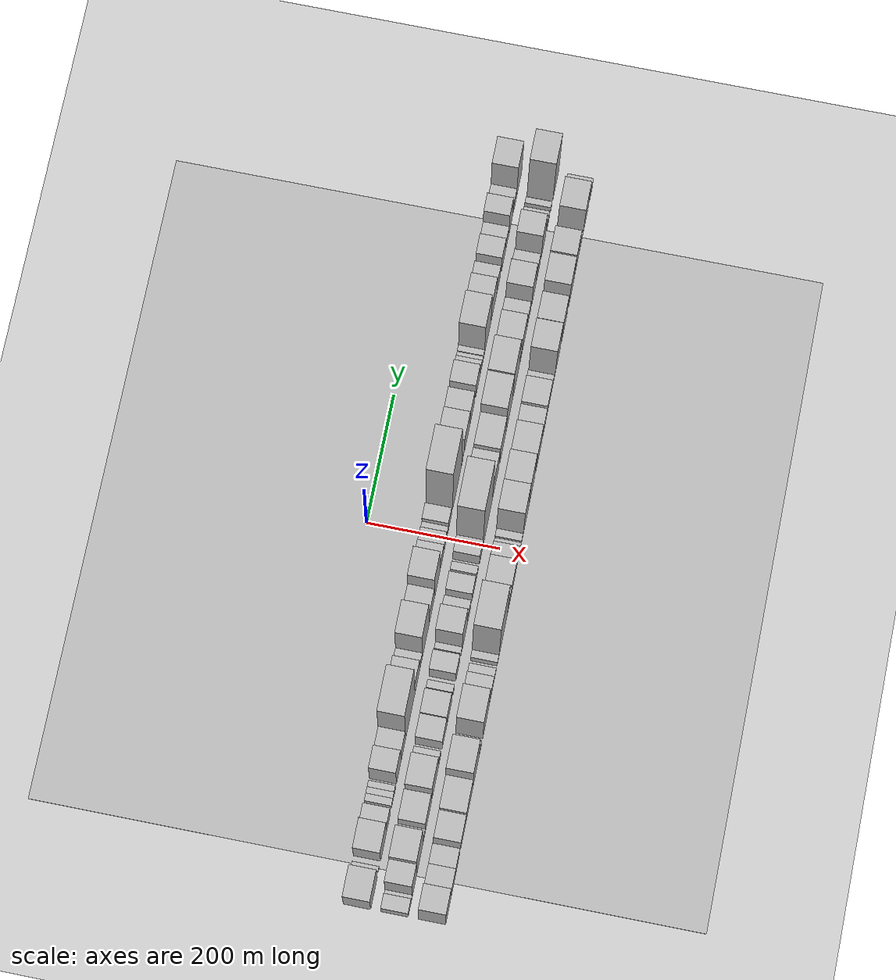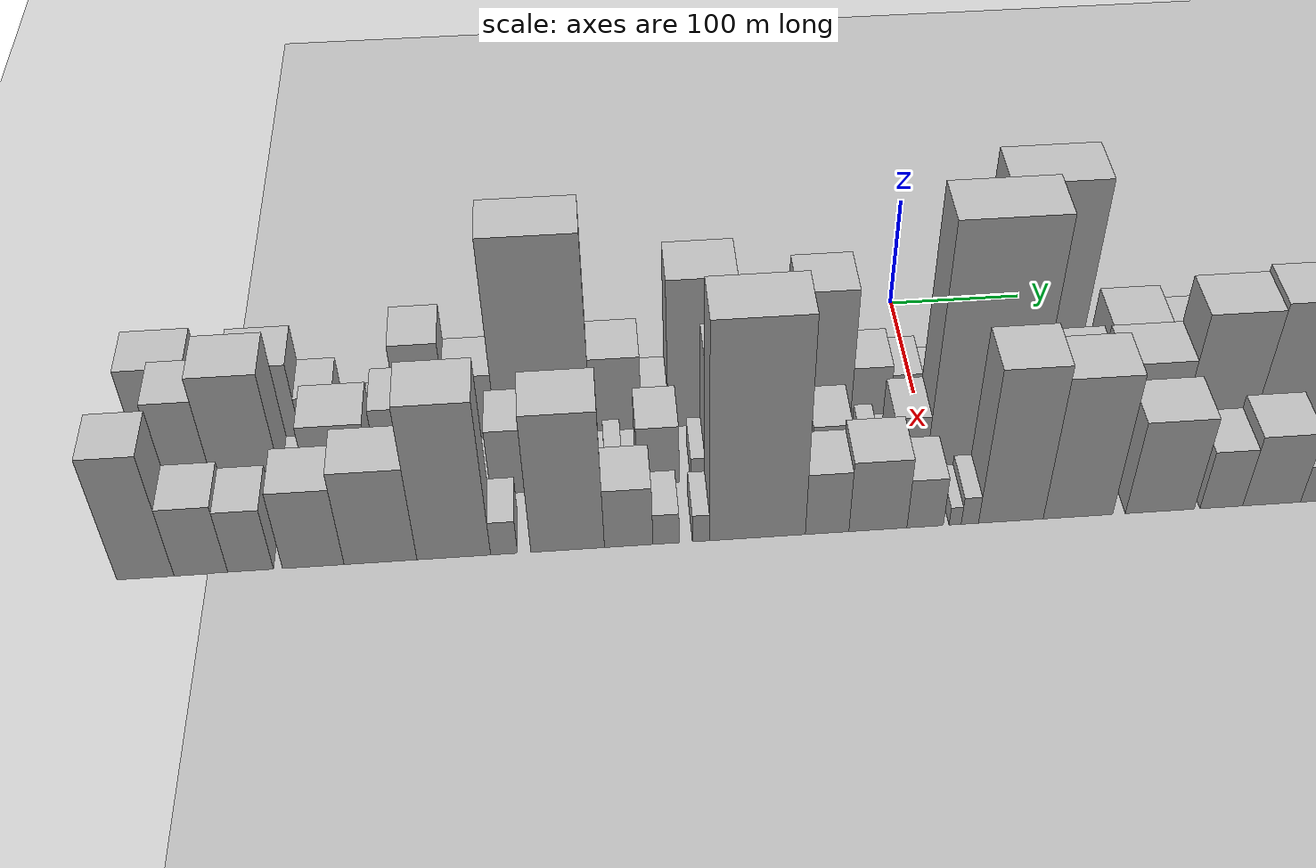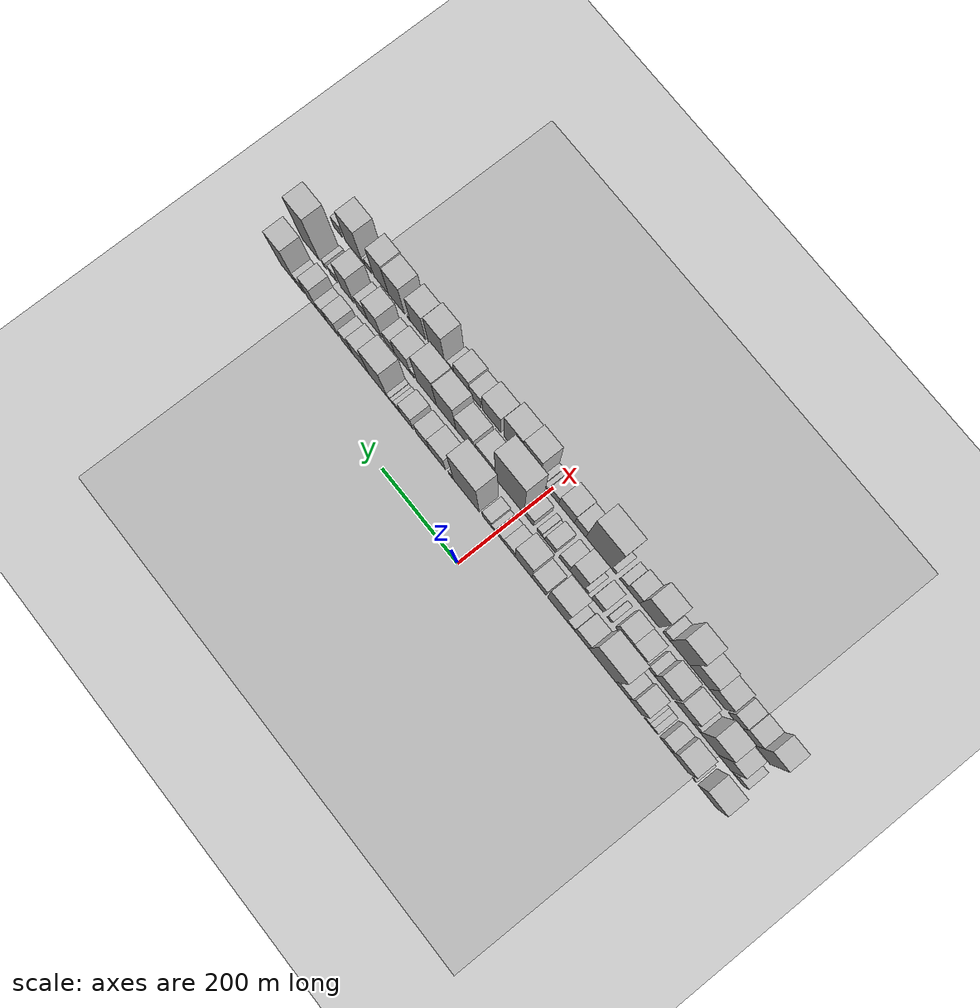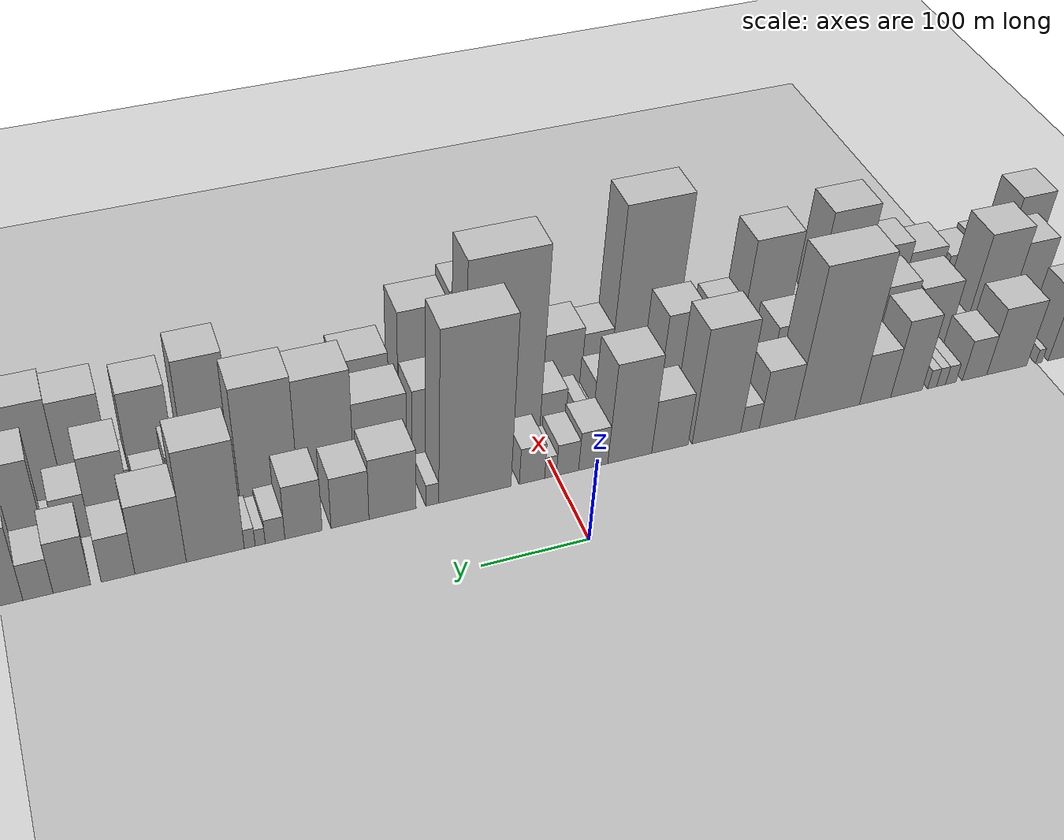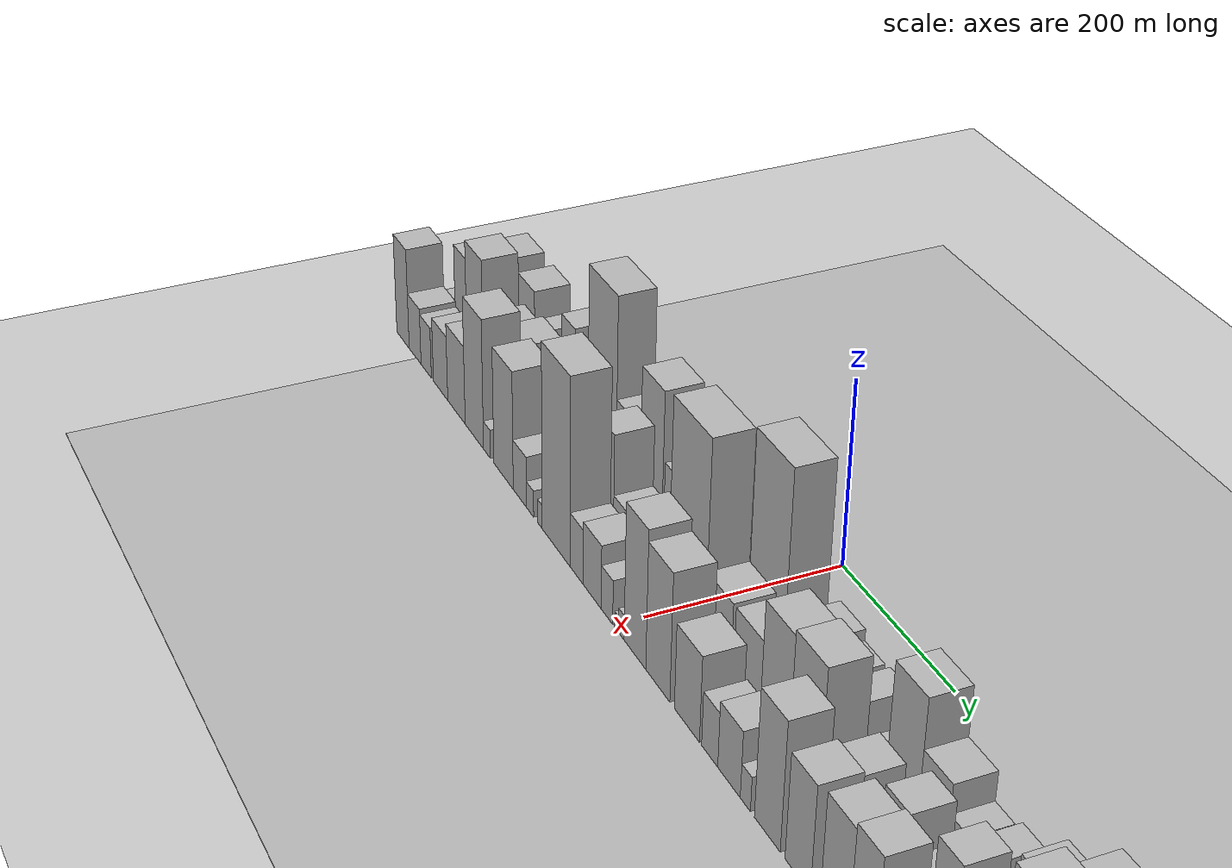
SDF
<?xml version="1.0" encoding="utf-8"?>

<sdf version="1.6">

   <world name="default">

      <gui fullscreen="0">

         <camera name="user_camera">

            <pose>-15 0 4.57585 0 0 0</pose>

            <view_controller>orbit</view_controller>

         </camera>

      </gui>

      <scene>

         <sky>

           <clouds>

             <speed>12</speed>

           </clouds>

         </sky>

         <ambient>0.4 0.4 0.4 1</ambient>

         <background>0.7 0.7 0.7 1</background>

         <shadows>1</shadows>

      </scene>

      <gravity>0 0 -9.8066</gravity>

      <magnetic_field>6e-06 2.3e-05 -4.2e-05</magnetic_field>

      <physics default="0" name="default_physics" type="ode">

         <ode>

            <solver>

               <type>quick</type>

               <iters>10</iters>

               <sor>1.0</sor>

               <use_dynamic_moi_rescaling>0</use_dynamic_moi_rescaling>

            </solver>

            <constraints>

               <cfm>0</cfm>

               <erp>0.2</erp>

               <contact_max_correcting_vel>100</contact_max_correcting_vel>

               <contact_surface_layer>0.001</contact_surface_layer>

            </constraints>

         </ode>

         <max_step_size>0.004</max_step_size>

         <real_time_factor>1</real_time_factor>

         <real_time_update_rate>250</real_time_update_rate>

      </physics>

      <light name="sun" type="directional">

         <cast_shadows>1</cast_shadows>

         <pose>0 0 10 0 0 0</pose>

         <diffuse>0.8 0.8 0.8 1</diffuse>

         <specular>0.2 0.2 0.2 1</specular>

         <attenuation>

            <range>1000</range>

            <constant>0.9</constant>

            <linear>0.01</linear>

            <quadratic>0.001</quadratic>

         </attenuation>

         <direction>-0.5 0.1 -0.9</direction>

      </light>

      <include>

         <name>ground_plane_1</name>

         <uri>model://HANNAS_ground_plane</uri>

         <pose>0 0 0  0 0 0</pose>

      </include>

      <include>

         <name>ground_plane_2</name>

         <uri>model://HANNAS_ground_plane</uri>

         <pose>100 0 0  0 0 0</pose>

      </include>

      <model name="building_1">

         <static>1</static>

         <pose frame="">100.0000 -536.5334 0 0.000000 0.000000 0.000000</pose>

         <link name="link">

            <pose frame="">0 0 43.50 0 0 0</pose>

            <collision name="collision">

               <geometry>

                  <box>

                     <size>40.0000 46.9333 87.0000</size>

                  </box>

               </geometry>

               <max_contacts>10</max_contacts>

               <surface>

                  <contact>

                     <ode/>

                  </contact>

                  <bounce/>

                  <friction>

                     <torsional>

                        <ode/>

                     </torsional>

                     <ode/>

                  </friction>

               </surface>

            </collision>

            <visual name="visual">

               <cast_shadows>0</cast_shadows>

               <geometry>

                  <box>

                     <size>40.0000 46.9333 87.0000</size>

                  </box>

               </geometry>

               <material>

                  <script>

                     <uri>model://HANNAS_wall/materials/scripts</uri>

                     <uri>model://HANNAS_wall/materials/textures</uri>

                     <name>vrc/HANNAS_wall</name>

                  </script>

               </material>

            </visual>

            <self_collide>0</self_collide>

            <enable_wind>0</enable_wind>

            <kinematic>0</kinematic>

         </link>

      </model>

      <model name="building_2">

         <static>1</static>

         <pose frame="">100.0000 -502.4519 0 0.000000 0.000000 0.000000</pose>

         <link name="link">

            <pose frame="">0 0 9.00 0 0 0</pose>

            <collision name="collision">

               <geometry>

                  <box>

                     <size>40.0000 7.2296 18.0000</size>

                  </box>

               </geometry>

               <max_contacts>10</max_contacts>

               <surface>

                  <contact>

                     <ode/>

                  </contact>

                  <bounce/>

                  <friction>

                     <torsional>

                        <ode/>

                     </torsional>

                     <ode/>

                  </friction>

               </surface>

            </collision>

            <visual name="visual">

               <cast_shadows>0</cast_shadows>

               <geometry>

                  <box>

                     <size>40.0000 7.2296 18.0000</size>

                  </box>

               </geometry>

               <material>

                  <script>

                     <uri>model://HANNAS_wall/materials/scripts</uri>

                     <uri>model://HANNAS_wall/materials/textures</uri>

                     <name>vrc/HANNAS_wall</name>

                  </script>

               </material>

            </visual>

            <self_collide>0</self_collide>

            <enable_wind>0</enable_wind>

            <kinematic>0</kinematic>

         </link>

      </model>

      <model name="building_3">

         <static>1</static>

         <pose frame="">100.0000 -466.6403 0 0.000000 0.000000 0.000000</pose>

         <link name="link">

            <pose frame="">0 0 42.00 0 0 0</pose>

            <collision name="collision">

               <geometry>

                  <box>

                     <size>40.0000 44.3936 84.0000</size>

                  </box>

               </geometry>

               <max_contacts>10</max_contacts>

               <surface>

                  <contact>

                     <ode/>

                  </contact>

                  <bounce/>

                  <friction>

                     <torsional>

                        <ode/>

                     </torsional>

                     <ode/>

                  </friction>

               </surface>

            </collision>

            <visual name="visual">

               <cast_shadows>0</cast_shadows>

               <geometry>

                  <box>

                     <size>40.0000 44.3936 84.0000</size>

                  </box>

               </geometry>

               <material>

                  <script>

                     <uri>model://HANNAS_wall/materials/scripts</uri>

                     <uri>model://HANNAS_wall/materials/textures</uri>

                     <name>vrc/HANNAS_wall</name>

                  </script>

               </material>

            </visual>

            <self_collide>0</self_collide>

            <enable_wind>0</enable_wind>

            <kinematic>0</kinematic>

         </link>

      </model>

      <model name="building_4">

         <static>1</static>

         <pose frame="">100.0000 -431.0699 0 0.000000 0.000000 0.000000</pose>

         <link name="link">

            <pose frame="">0 0 25.50 0 0 0</pose>

            <collision name="collision">

               <geometry>

                  <box>

                     <size>40.0000 26.7471 51.0000</size>

                  </box>

               </geometry>

               <max_contacts>10</max_contacts>

               <surface>

                  <contact>

                     <ode/>

                  </contact>

                  <bounce/>

                  <friction>

                     <torsional>

                        <ode/>

                     </torsional>

                     <ode/>

                  </friction>

               </surface>

            </collision>

            <visual name="visual">

               <cast_shadows>0</cast_shadows>

               <geometry>

                  <box>

                     <size>40.0000 26.7471 51.0000</size>

                  </box>

               </geometry>

               <material>

                  <script>

                     <uri>model://HANNAS_wall/materials/scripts</uri>

                     <uri>model://HANNAS_wall/materials/textures</uri>

                     <name>vrc/HANNAS_wall</name>

                  </script>

               </material>

            </visual>

            <self_collide>0</self_collide>

            <enable_wind>0</enable_wind>

            <kinematic>0</kinematic>

         </link>

      </model>

      <model name="building_5">

         <static>1</static>

         <pose frame="">100.0000 -405.0169 0 0.000000 0.000000 0.000000</pose>

         <link name="link">

            <pose frame="">0 0 12.00 0 0 0</pose>

            <collision name="collision">

               <geometry>

                  <box>

                     <size>40.0000 11.3590 24.0000</size>

                  </box>

               </geometry>

               <max_contacts>10</max_contacts>

               <surface>

                  <contact>

                     <ode/>

                  </contact>

                  <bounce/>

                  <friction>

                     <torsional>

                        <ode/>

                     </torsional>

                     <ode/>

                  </friction>

               </surface>

            </collision>

            <visual name="visual">

               <cast_shadows>0</cast_shadows>

               <geometry>

                  <box>

                     <size>40.0000 11.3590 24.0000</size>

                  </box>

               </geometry>

               <material>

                  <script>

                     <uri>model://HANNAS_wall/materials/scripts</uri>

                     <uri>model://HANNAS_wall/materials/textures</uri>

                     <name>vrc/HANNAS_wall</name>

                  </script>

               </material>

            </visual>

            <self_collide>0</self_collide>

            <enable_wind>0</enable_wind>

            <kinematic>0</kinematic>

         </link>

      </model>

      <model name="building_6">

         <static>1</static>

         <pose frame="">100.0000 -394.4631 0 0.000000 0.000000 0.000000</pose>

         <link name="link">

            <pose frame="">0 0 12.00 0 0 0</pose>

            <collision name="collision">

               <geometry>

                  <box>

                     <size>40.0000 9.7486 24.0000</size>

                  </box>

               </geometry>

               <max_contacts>10</max_contacts>

               <surface>

                  <contact>

                     <ode/>

                  </contact>

                  <bounce/>

                  <friction>

                     <torsional>

                        <ode/>

                     </torsional>

                     <ode/>

                  </friction>

               </surface>

            </collision>

            <visual name="visual">

               <cast_shadows>0</cast_shadows>

               <geometry>

                  <box>

                     <size>40.0000 9.7486 24.0000</size>

                  </box>

               </geometry>

               <material>

                  <script>

                     <uri>model://HANNAS_wall/materials/scripts</uri>

                     <uri>model://HANNAS_wall/materials/textures</uri>

                     <name>vrc/HANNAS_wall</name>

                  </script>

               </material>

            </visual>

            <self_collide>0</self_collide>

            <enable_wind>0</enable_wind>

            <kinematic>0</kinematic>

         </link>

      </model>

      <model name="building_7">

         <static>1</static>

         <pose frame="">100.0000 -384.7748 0 0.000000 0.000000 0.000000</pose>

         <link name="link">

            <pose frame="">0 0 12.00 0 0 0</pose>

            <collision name="collision">

               <geometry>

                  <box>

                     <size>40.0000 9.6279 24.0000</size>

                  </box>

               </geometry>

               <max_contacts>10</max_contacts>

               <surface>

                  <contact>

                     <ode/>

                  </contact>

                  <bounce/>

                  <friction>

                     <torsional>

                        <ode/>

                     </torsional>

                     <ode/>

                  </friction>

               </surface>

            </collision>

            <visual name="visual">

               <cast_shadows>0</cast_shadows>

               <geometry>

                  <box>

                     <size>40.0000 9.6279 24.0000</size>

                  </box>

               </geometry>

               <material>

                  <script>

                     <uri>model://HANNAS_wall/materials/scripts</uri>

                     <uri>model://HANNAS_wall/materials/textures</uri>

                     <name>vrc/HANNAS_wall</name>

                  </script>

               </material>

            </visual>

            <self_collide>0</self_collide>

            <enable_wind>0</enable_wind>

            <kinematic>0</kinematic>

         </link>

      </model>

      <model name="building_8">

         <static>1</static>

         <pose frame="">100.0000 -357.0146 0 0.000000 0.000000 0.000000</pose>

         <link name="link">

            <pose frame="">0 0 48.00 0 0 0</pose>

            <collision name="collision">

               <geometry>

                  <box>

                     <size>40.0000 33.8926 96.0000</size>

                  </box>

               </geometry>

               <max_contacts>10</max_contacts>

               <surface>

                  <contact>

                     <ode/>

                  </contact>

                  <bounce/>

                  <friction>

                     <torsional>

                        <ode/>

                     </torsional>

                     <ode/>

                  </friction>

               </surface>

            </collision>

            <visual name="visual">

               <cast_shadows>0</cast_shadows>

               <geometry>

                  <box>

                     <size>40.0000 33.8926 96.0000</size>

                  </box>

               </geometry>

               <material>

                  <script>

                     <uri>model://HANNAS_wall/materials/scripts</uri>

                     <uri>model://HANNAS_wall/materials/textures</uri>

                     <name>vrc/HANNAS_wall</name>

                  </script>

               </material>

            </visual>

            <self_collide>0</self_collide>

            <enable_wind>0</enable_wind>

            <kinematic>0</kinematic>

         </link>

      </model>

      <model name="building_9">

         <static>1</static>

         <pose frame="">100.0000 -323.3903 0 0.000000 0.000000 0.000000</pose>

         <link name="link">

            <pose frame="">0 0 31.50 0 0 0</pose>

            <collision name="collision">

               <geometry>

                  <box>

                     <size>40.0000 33.3559 63.0000</size>

                  </box>

               </geometry>

               <max_contacts>10</max_contacts>

               <surface>

                  <contact>

                     <ode/>

                  </contact>

                  <bounce/>

                  <friction>

                     <torsional>

                        <ode/>

                     </torsional>

                     <ode/>

                  </friction>

               </surface>

            </collision>

            <visual name="visual">

               <cast_shadows>0</cast_shadows>

               <geometry>

                  <box>

                     <size>40.0000 33.3559 63.0000</size>

                  </box>

               </geometry>

               <material>

                  <script>

                     <uri>model://HANNAS_wall/materials/scripts</uri>

                     <uri>model://HANNAS_wall/materials/textures</uri>

                     <name>vrc/HANNAS_wall</name>

                  </script>

               </material>

            </visual>

            <self_collide>0</self_collide>

            <enable_wind>0</enable_wind>

            <kinematic>0</kinematic>

         </link>

      </model>

      <model name="building_10">

         <static>1</static>

         <pose frame="">100.0000 -272.7068 0 0.000000 0.000000 0.000000</pose>

         <link name="link">

            <pose frame="">0 0 93.00 0 0 0</pose>

            <collision name="collision">

               <geometry>

                  <box>

                     <size>40.0000 68.0113 186.0000</size>

                  </box>

               </geometry>

               <max_contacts>10</max_contacts>

               <surface>

                  <contact>

                     <ode/>

                  </contact>

                  <bounce/>

                  <friction>

                     <torsional>

                        <ode/>

                     </torsional>

                     <ode/>

                  </friction>

               </surface>

            </collision>

            <visual name="visual">

               <cast_shadows>0</cast_shadows>

               <geometry>

                  <box>

                     <size>40.0000 68.0113 186.0000</size>

                  </box>

               </geometry>

               <material>

                  <script>

                     <uri>model://HANNAS_wall/materials/scripts</uri>

                     <uri>model://HANNAS_wall/materials/textures</uri>

                     <name>vrc/HANNAS_wall</name>

                  </script>

               </material>

            </visual>

            <self_collide>0</self_collide>

            <enable_wind>0</enable_wind>

            <kinematic>0</kinematic>

         </link>

      </model>

      <model name="building_11">

         <static>1</static>

         <pose frame="">100.0000 -220.4346 0 0.000000 0.000000 0.000000</pose>

         <link name="link">

            <pose frame="">0 0 36.00 0 0 0</pose>

            <collision name="collision">

               <geometry>

                  <box>

                     <size>40.0000 36.5331 72.0000</size>

                  </box>

               </geometry>

               <max_contacts>10</max_contacts>

               <surface>

                  <contact>

                     <ode/>

                  </contact>

                  <bounce/>

                  <friction>

                     <torsional>

                        <ode/>

                     </torsional>

                     <ode/>

                  </friction>

               </surface>

            </collision>

            <visual name="visual">

               <cast_shadows>0</cast_shadows>

               <geometry>

                  <box>

                     <size>40.0000 36.5331 72.0000</size>

                  </box>

               </geometry>

               <material>

                  <script>

                     <uri>model://HANNAS_wall/materials/scripts</uri>

                     <uri>model://HANNAS_wall/materials/textures</uri>

                     <name>vrc/HANNAS_wall</name>

                  </script>

               </material>

            </visual>

            <self_collide>0</self_collide>

            <enable_wind>0</enable_wind>

            <kinematic>0</kinematic>

         </link>

      </model>

      <model name="building_12">

         <static>1</static>

         <pose frame="">100.0000 -192.5128 0 0.000000 0.000000 0.000000</pose>

         <link name="link">

            <pose frame="">0 0 16.50 0 0 0</pose>

            <collision name="collision">

               <geometry>

                  <box>

                     <size>40.0000 19.3104 33.0000</size>

                  </box>

               </geometry>

               <max_contacts>10</max_contacts>

               <surface>

                  <contact>

                     <ode/>

                  </contact>

                  <bounce/>

                  <friction>

                     <torsional>

                        <ode/>

                     </torsional>

                     <ode/>

                  </friction>

               </surface>

            </collision>

            <visual name="visual">

               <cast_shadows>0</cast_shadows>

               <geometry>

                  <box>

                     <size>40.0000 19.3104 33.0000</size>

                  </box>

               </geometry>

               <material>

                  <script>

                     <uri>model://HANNAS_wall/materials/scripts</uri>

                     <uri>model://HANNAS_wall/materials/textures</uri>

                     <name>vrc/HANNAS_wall</name>

                  </script>

               </material>

            </visual>

            <self_collide>0</self_collide>

            <enable_wind>0</enable_wind>

            <kinematic>0</kinematic>

         </link>

      </model>

      <model name="building_13">

         <static>1</static>

         <pose frame="">100.0000 -158.2269 0 0.000000 0.000000 0.000000</pose>

         <link name="link">

            <pose frame="">0 0 70.50 0 0 0</pose>

            <collision name="collision">

               <geometry>

                  <box>

                     <size>40.0000 49.2615 141.0000</size>

                  </box>

               </geometry>

               <max_contacts>10</max_contacts>

               <surface>

                  <contact>

                     <ode/>

                  </contact>

                  <bounce/>

                  <friction>

                     <torsional>

                        <ode/>

                     </torsional>

                     <ode/>

                  </friction>

               </surface>

            </collision>

            <visual name="visual">

               <cast_shadows>0</cast_shadows>

               <geometry>

                  <box>

                     <size>40.0000 49.2615 141.0000</size>

                  </box>

               </geometry>

               <material>

                  <script>

                     <uri>model://HANNAS_wall/materials/scripts</uri>

                     <uri>model://HANNAS_wall/materials/textures</uri>

                     <name>vrc/HANNAS_wall</name>

                  </script>

               </material>

            </visual>

            <self_collide>0</self_collide>

            <enable_wind>0</enable_wind>

            <kinematic>0</kinematic>

         </link>

      </model>

      <model name="building_14">

         <static>1</static>

         <pose frame="">100.0000 -111.2981 0 0.000000 0.000000 0.000000</pose>

         <link name="link">

            <pose frame="">0 0 33.00 0 0 0</pose>

            <collision name="collision">

               <geometry>

                  <box>

                     <size>40.0000 36.5961 66.0000</size>

                  </box>

               </geometry>

               <max_contacts>10</max_contacts>

               <surface>

                  <contact>

                     <ode/>

                  </contact>

                  <bounce/>

                  <friction>

                     <torsional>

                        <ode/>

                     </torsional>

                     <ode/>

                  </friction>

               </surface>

            </collision>

            <visual name="visual">

               <cast_shadows>0</cast_shadows>

               <geometry>

                  <box>

                     <size>40.0000 36.5961 66.0000</size>

                  </box>

               </geometry>

               <material>

                  <script>

                     <uri>model://HANNAS_wall/materials/scripts</uri>

                     <uri>model://HANNAS_wall/materials/textures</uri>

                     <name>vrc/HANNAS_wall</name>

                  </script>

               </material>

            </visual>

            <self_collide>0</self_collide>

            <enable_wind>0</enable_wind>

            <kinematic>0</kinematic>

         </link>

      </model>

      <model name="building_15">

         <static>1</static>

         <pose frame="">100.0000 -71.2497 0 0.000000 0.000000 0.000000</pose>

         <link name="link">

            <pose frame="">0 0 61.50 0 0 0</pose>

            <collision name="collision">

               <geometry>

                  <box>

                     <size>40.0000 43.5008 123.0000</size>

                  </box>

               </geometry>

               <max_contacts>10</max_contacts>

               <surface>

                  <contact>

                     <ode/>

                  </contact>

                  <bounce/>

                  <friction>

                     <torsional>

                        <ode/>

                     </torsional>

                     <ode/>

                  </friction>

               </surface>

            </collision>

            <visual name="visual">

               <cast_shadows>0</cast_shadows>

               <geometry>

                  <box>

                     <size>40.0000 43.5008 123.0000</size>

                  </box>

               </geometry>

               <material>

                  <script>

                     <uri>model://HANNAS_wall/materials/scripts</uri>

                     <uri>model://HANNAS_wall/materials/textures</uri>

                     <name>vrc/HANNAS_wall</name>

                  </script>

               </material>

            </visual>

            <self_collide>0</self_collide>

            <enable_wind>0</enable_wind>

            <kinematic>0</kinematic>

         </link>

      </model>

      <model name="building_16">

         <static>1</static>

         <pose frame="">100.0000 -35.2261 0 0.000000 0.000000 0.000000</pose>

         <link name="link">

            <pose frame="">0 0 24.00 0 0 0</pose>

            <collision name="collision">

               <geometry>

                  <box>

                     <size>40.0000 28.5463 48.0000</size>

                  </box>

               </geometry>

               <max_contacts>10</max_contacts>

               <surface>

                  <contact>

                     <ode/>

                  </contact>

                  <bounce/>

                  <friction>

                     <torsional>

                        <ode/>

                     </torsional>

                     <ode/>

                  </friction>

               </surface>

            </collision>

            <visual name="visual">

               <cast_shadows>0</cast_shadows>

               <geometry>

                  <box>

                     <size>40.0000 28.5463 48.0000</size>

                  </box>

               </geometry>

               <material>

                  <script>

                     <uri>model://HANNAS_wall/materials/scripts</uri>

                     <uri>model://HANNAS_wall/materials/textures</uri>

                     <name>vrc/HANNAS_wall</name>

                  </script>

               </material>

            </visual>

            <self_collide>0</self_collide>

            <enable_wind>0</enable_wind>

            <kinematic>0</kinematic>

         </link>

      </model>

      <model name="building_17">

         <static>1</static>

         <pose frame="">100.0000 -10.1264 0 0.000000 0.000000 0.000000</pose>

         <link name="link">

            <pose frame="">0 0 19.50 0 0 0</pose>

            <collision name="collision">

               <geometry>

                  <box>

                     <size>40.0000 21.6532 39.0000</size>

                  </box>

               </geometry>

               <max_contacts>10</max_contacts>

               <surface>

                  <contact>

                     <ode/>

                  </contact>

                  <bounce/>

                  <friction>

                     <torsional>

                        <ode/>

                     </torsional>

                     <ode/>

                  </friction>

               </surface>

            </collision>

            <visual name="visual">

               <cast_shadows>0</cast_shadows>

               <geometry>

                  <box>

                     <size>40.0000 21.6532 39.0000</size>

                  </box>

               </geometry>

               <material>

                  <script>

                     <uri>model://HANNAS_wall/materials/scripts</uri>

                     <uri>model://HANNAS_wall/materials/textures</uri>

                     <name>vrc/HANNAS_wall</name>

                  </script>

               </material>

            </visual>

            <self_collide>0</self_collide>

            <enable_wind>0</enable_wind>

            <kinematic>0</kinematic>

         </link>

      </model>

      <model name="building_18">

         <static>1</static>

         <pose frame="">100.0000 6.3788 0 0.000000 0.000000 0.000000</pose>

         <link name="link">

            <pose frame="">0 0 13.50 0 0 0</pose>

            <collision name="collision">

               <geometry>

                  <box>

                     <size>40.0000 11.3573 27.0000</size>

                  </box>

               </geometry>

               <max_contacts>10</max_contacts>

               <surface>

                  <contact>

                     <ode/>

                  </contact>

                  <bounce/>

                  <friction>

                     <torsional>

                        <ode/>

                     </torsional>

                     <ode/>

                  </friction>

               </surface>

            </collision>

            <visual name="visual">

               <cast_shadows>0</cast_shadows>

               <geometry>

                  <box>

                     <size>40.0000 11.3573 27.0000</size>

                  </box>

               </geometry>

               <material>

                  <script>

                     <uri>model://HANNAS_wall/materials/scripts</uri>

                     <uri>model://HANNAS_wall/materials/textures</uri>

                     <name>vrc/HANNAS_wall</name>

                  </script>

               </material>

            </visual>

            <self_collide>0</self_collide>

            <enable_wind>0</enable_wind>

            <kinematic>0</kinematic>

         </link>

      </model>

      <model name="building_19">

         <static>1</static>

         <pose frame="">100.0000 24.2329 0 0.000000 0.000000 0.000000</pose>

         <link name="link">

            <pose frame="">0 0 22.50 0 0 0</pose>

            <collision name="collision">

               <geometry>

                  <box>

                     <size>40.0000 24.3510 45.0000</size>

                  </box>

               </geometry>

               <max_contacts>10</max_contacts>

               <surface>

                  <contact>

                     <ode/>

                  </contact>

                  <bounce/>

                  <friction>

                     <torsional>

                        <ode/>

                     </torsional>

                     <ode/>

                  </friction>

               </surface>

            </collision>

            <visual name="visual">

               <cast_shadows>0</cast_shadows>

               <geometry>

                  <box>

                     <size>40.0000 24.3510 45.0000</size>

                  </box>

               </geometry>

               <material>

                  <script>

                     <uri>model://HANNAS_wall/materials/scripts</uri>

                     <uri>model://HANNAS_wall/materials/textures</uri>

                     <name>vrc/HANNAS_wall</name>

                  </script>

               </material>

            </visual>

            <self_collide>0</self_collide>

            <enable_wind>0</enable_wind>

            <kinematic>0</kinematic>

         </link>

      </model>

      <model name="building_20">

         <static>1</static>

         <pose frame="">100.0000 78.5924 0 0.000000 0.000000 0.000000</pose>

         <link name="link">

            <pose frame="">0 0 103.50 0 0 0</pose>

            <collision name="collision">

               <geometry>

                  <box>

                     <size>40.0000 68.3679 207.0000</size>

                  </box>

               </geometry>

               <max_contacts>10</max_contacts>

               <surface>

                  <contact>

                     <ode/>

                  </contact>

                  <bounce/>

                  <friction>

                     <torsional>

                        <ode/>

                     </torsional>

                     <ode/>

                  </friction>

               </surface>

            </collision>

            <visual name="visual">

               <cast_shadows>0</cast_shadows>

               <geometry>

                  <box>

                     <size>40.0000 68.3679 207.0000</size>

                  </box>

               </geometry>

               <material>

                  <script>

                     <uri>model://HANNAS_wall/materials/scripts</uri>

                     <uri>model://HANNAS_wall/materials/textures</uri>

                     <name>vrc/HANNAS_wall</name>

                  </script>

               </material>

            </visual>

            <self_collide>0</self_collide>

            <enable_wind>0</enable_wind>

            <kinematic>0</kinematic>

         </link>

      </model>

      <model name="building_21">

         <static>1</static>

         <pose frame="">100.0000 118.8101 0 0.000000 0.000000 0.000000</pose>

         <link name="link">

            <pose frame="">0 0 13.50 0 0 0</pose>

            <collision name="collision">

               <geometry>

                  <box>

                     <size>40.0000 12.0674 27.0000</size>

                  </box>

               </geometry>

               <max_contacts>10</max_contacts>

               <surface>

                  <contact>

                     <ode/>

                  </contact>

                  <bounce/>

                  <friction>

                     <torsional>

                        <ode/>

                     </torsional>

                     <ode/>

                  </friction>

               </surface>

            </collision>

            <visual name="visual">

               <cast_shadows>0</cast_shadows>

               <geometry>

                  <box>

                     <size>40.0000 12.0674 27.0000</size>

                  </box>

               </geometry>

               <material>

                  <script>

                     <uri>model://HANNAS_wall/materials/scripts</uri>

                     <uri>model://HANNAS_wall/materials/textures</uri>

                     <name>vrc/HANNAS_wall</name>

                  </script>

               </material>

            </visual>

            <self_collide>0</self_collide>

            <enable_wind>0</enable_wind>

            <kinematic>0</kinematic>

         </link>

      </model>

      <model name="building_22">

         <static>1</static>

         <pose frame="">100.0000 155.6362 0 0.000000 0.000000 0.000000</pose>

         <link name="link">

            <pose frame="">0 0 37.50 0 0 0</pose>

            <collision name="collision">

               <geometry>

                  <box>

                     <size>40.0000 43.5848 75.0000</size>

                  </box>

               </geometry>

               <max_contacts>10</max_contacts>

               <surface>

                  <contact>

                     <ode/>

                  </contact>

                  <bounce/>

                  <friction>

                     <torsional>

                        <ode/>

                     </torsional>

                     <ode/>

                  </friction>

               </surface>

            </collision>

            <visual name="visual">

               <cast_shadows>0</cast_shadows>

               <geometry>

                  <box>

                     <size>40.0000 43.5848 75.0000</size>

                  </box>

               </geometry>

               <material>

                  <script>

                     <uri>model://HANNAS_wall/materials/scripts</uri>

                     <uri>model://HANNAS_wall/materials/textures</uri>

                     <name>vrc/HANNAS_wall</name>

                  </script>

               </material>

            </visual>

            <self_collide>0</self_collide>

            <enable_wind>0</enable_wind>

            <kinematic>0</kinematic>

         </link>

      </model>

      <model name="building_23">

         <static>1</static>

         <pose frame="">100.0000 194.7399 0 0.000000 0.000000 0.000000</pose>

         <link name="link">

            <pose frame="">0 0 31.50 0 0 0</pose>

            <collision name="collision">

               <geometry>

                  <box>

                     <size>40.0000 34.6225 63.0000</size>

                  </box>

               </geometry>

               <max_contacts>10</max_contacts>

               <surface>

                  <contact>

                     <ode/>

                  </contact>

                  <bounce/>

                  <friction>

                     <torsional>

                        <ode/>

                     </torsional>

                     <ode/>

                  </friction>

               </surface>

            </collision>

            <visual name="visual">

               <cast_shadows>0</cast_shadows>

               <geometry>

                  <box>

                     <size>40.0000 34.6225 63.0000</size>

                  </box>

               </geometry>

               <material>

                  <script>

                     <uri>model://HANNAS_wall/materials/scripts</uri>

                     <uri>model://HANNAS_wall/materials/textures</uri>

                     <name>vrc/HANNAS_wall</name>

                  </script>

               </material>

            </visual>

            <self_collide>0</self_collide>

            <enable_wind>0</enable_wind>

            <kinematic>0</kinematic>

         </link>

      </model>

      <model name="building_24">

         <static>1</static>

         <pose frame="">100.0000 236.9002 0 0.000000 0.000000 0.000000</pose>

         <link name="link">

            <pose frame="">0 0 33.00 0 0 0</pose>

            <collision name="collision">

               <geometry>

                  <box>

                     <size>40.0000 33.6981 66.0000</size>

                  </box>

               </geometry>

               <max_contacts>10</max_contacts>

               <surface>

                  <contact>

                     <ode/>

                  </contact>

                  <bounce/>

                  <friction>

                     <torsional>

                        <ode/>

                     </torsional>

                     <ode/>

                  </friction>

               </surface>

            </collision>

            <visual name="visual">

               <cast_shadows>0</cast_shadows>

               <geometry>

                  <box>

                     <size>40.0000 33.6981 66.0000</size>

                  </box>

               </geometry>

               <material>

                  <script>

                     <uri>model://HANNAS_wall/materials/scripts</uri>

                     <uri>model://HANNAS_wall/materials/textures</uri>

                     <name>vrc/HANNAS_wall</name>

                  </script>

               </material>

            </visual>

            <self_collide>0</self_collide>

            <enable_wind>0</enable_wind>

            <kinematic>0</kinematic>

         </link>

      </model>

      <model name="building_25">

         <static>1</static>

         <pose frame="">100.0000 262.5247 0 0.000000 0.000000 0.000000</pose>

         <link name="link">

            <pose frame="">0 0 15.00 0 0 0</pose>

            <collision name="collision">

               <geometry>

                  <box>

                     <size>40.0000 17.5508 30.0000</size>

                  </box>

               </geometry>

               <max_contacts>10</max_contacts>

               <surface>

                  <contact>

                     <ode/>

                  </contact>

                  <bounce/>

                  <friction>

                     <torsional>

                        <ode/>

                     </torsional>

                     <ode/>

                  </friction>

               </surface>

            </collision>

            <visual name="visual">

               <cast_shadows>0</cast_shadows>

               <geometry>

                  <box>

                     <size>40.0000 17.5508 30.0000</size>

                  </box>

               </geometry>

               <material>

                  <script>

                     <uri>model://HANNAS_wall/materials/scripts</uri>

                     <uri>model://HANNAS_wall/materials/textures</uri>

                     <name>vrc/HANNAS_wall</name>

                  </script>

               </material>

            </visual>

            <self_collide>0</self_collide>

            <enable_wind>0</enable_wind>

            <kinematic>0</kinematic>

         </link>

      </model>

      <model name="building_26">

         <static>1</static>

         <pose frame="">100.0000 275.7841 0 0.000000 0.000000 0.000000</pose>

         <link name="link">

            <pose frame="">0 0 10.50 0 0 0</pose>

            <collision name="collision">

               <geometry>

                  <box>

                     <size>40.0000 8.9680 21.0000</size>

                  </box>

               </geometry>

               <max_contacts>10</max_contacts>

               <surface>

                  <contact>

                     <ode/>

                  </contact>

                  <bounce/>

                  <friction>

                     <torsional>

                        <ode/>

                     </torsional>

                     <ode/>

                  </friction>

               </surface>

            </collision>

            <visual name="visual">

               <cast_shadows>0</cast_shadows>

               <geometry>

                  <box>

                     <size>40.0000 8.9680 21.0000</size>

                  </box>

               </geometry>

               <material>

                  <script>

                     <uri>model://HANNAS_wall/materials/scripts</uri>

                     <uri>model://HANNAS_wall/materials/textures</uri>

                     <name>vrc/HANNAS_wall</name>

                  </script>

               </material>

            </visual>

            <self_collide>0</self_collide>

            <enable_wind>0</enable_wind>

            <kinematic>0</kinematic>

         </link>

      </model>

      <model name="building_27">

         <static>1</static>

         <pose frame="">100.0000 285.0695 0 0.000000 0.000000 0.000000</pose>

         <link name="link">

            <pose frame="">0 0 12.00 0 0 0</pose>

            <collision name="collision">

               <geometry>

                  <box>

                     <size>40.0000 9.6028 24.0000</size>

                  </box>

               </geometry>

               <max_contacts>10</max_contacts>

               <surface>

                  <contact>

                     <ode/>

                  </contact>

                  <bounce/>

                  <friction>

                     <torsional>

                        <ode/>

                     </torsional>

                     <ode/>

                  </friction>

               </surface>

            </collision>

            <visual name="visual">

               <cast_shadows>0</cast_shadows>

               <geometry>

                  <box>

                     <size>40.0000 9.6028 24.0000</size>

                  </box>

               </geometry>

               <material>

                  <script>

                     <uri>model://HANNAS_wall/materials/scripts</uri>

                     <uri>model://HANNAS_wall/materials/textures</uri>

                     <name>vrc/HANNAS_wall</name>

                  </script>

               </material>

            </visual>

            <self_collide>0</self_collide>

            <enable_wind>0</enable_wind>

            <kinematic>0</kinematic>

         </link>

      </model>

      <model name="building_28">

         <static>1</static>

         <pose frame="">100.0000 315.3543 0 0.000000 0.000000 0.000000</pose>

         <link name="link">

            <pose frame="">0 0 67.50 0 0 0</pose>

            <collision name="collision">

               <geometry>

                  <box>

                     <size>40.0000 50.9669 135.0000</size>

                  </box>

               </geometry>

               <max_contacts>10</max_contacts>

               <surface>

                  <contact>

                     <ode/>

                  </contact>

                  <bounce/>

                  <friction>

                     <torsional>

                        <ode/>

                     </torsional>

                     <ode/>

                  </friction>

               </surface>

            </collision>

            <visual name="visual">

               <cast_shadows>0</cast_shadows>

               <geometry>

                  <box>

                     <size>40.0000 50.9669 135.0000</size>

                  </box>

               </geometry>

               <material>

                  <script>

                     <uri>model://HANNAS_wall/materials/scripts</uri>

                     <uri>model://HANNAS_wall/materials/textures</uri>

                     <name>vrc/HANNAS_wall</name>

                  </script>

               </material>

            </visual>

            <self_collide>0</self_collide>

            <enable_wind>0</enable_wind>

            <kinematic>0</kinematic>

         </link>

      </model>

      <model name="building_29">

         <static>1</static>

         <pose frame="">100.0000 363.0574 0 0.000000 0.000000 0.000000</pose>

         <link name="link">

            <pose frame="">0 0 42.00 0 0 0</pose>

            <collision name="collision">

               <geometry>

                  <box>

                     <size>40.0000 44.4392 84.0000</size>

                  </box>

               </geometry>

               <max_contacts>10</max_contacts>

               <surface>

                  <contact>

                     <ode/>

                  </contact>

                  <bounce/>

                  <friction>

                     <torsional>

                        <ode/>

                     </torsional>

                     <ode/>

                  </friction>

               </surface>

            </collision>

            <visual name="visual">

               <cast_shadows>0</cast_shadows>

               <geometry>

                  <box>

                     <size>40.0000 44.4392 84.0000</size>

                  </box>

               </geometry>

               <material>

                  <script>

                     <uri>model://HANNAS_wall/materials/scripts</uri>

                     <uri>model://HANNAS_wall/materials/textures</uri>

                     <name>vrc/HANNAS_wall</name>

                  </script>

               </material>

            </visual>

            <self_collide>0</self_collide>

            <enable_wind>0</enable_wind>

            <kinematic>0</kinematic>

         </link>

      </model>

      <model name="building_30">

         <static>1</static>

         <pose frame="">100.0000 399.7521 0 0.000000 0.000000 0.000000</pose>

         <link name="link">

            <pose frame="">0 0 27.00 0 0 0</pose>

            <collision name="collision">

               <geometry>

                  <box>

                     <size>40.0000 28.9502 54.0000</size>

                  </box>

               </geometry>

               <max_contacts>10</max_contacts>

               <surface>

                  <contact>

                     <ode/>

                  </contact>

                  <bounce/>

                  <friction>

                     <torsional>

                        <ode/>

                     </torsional>

                     <ode/>

                  </friction>

               </surface>

            </collision>

            <visual name="visual">

               <cast_shadows>0</cast_shadows>

               <geometry>

                  <box>

                     <size>40.0000 28.9502 54.0000</size>

                  </box>

               </geometry>

               <material>

                  <script>

                     <uri>model://HANNAS_wall/materials/scripts</uri>

                     <uri>model://HANNAS_wall/materials/textures</uri>

                     <name>vrc/HANNAS_wall</name>

                  </script>

               </material>

            </visual>

            <self_collide>0</self_collide>

            <enable_wind>0</enable_wind>

            <kinematic>0</kinematic>

         </link>

      </model>

      <model name="building_31">

         <static>1</static>

         <pose frame="">100.0000 439.0768 0 0.000000 0.000000 0.000000</pose>

         <link name="link">

            <pose frame="">0 0 31.50 0 0 0</pose>

            <collision name="collision">

               <geometry>

                  <box>

                     <size>40.0000 31.6992 63.0000</size>

                  </box>

               </geometry>

               <max_contacts>10</max_contacts>

               <surface>

                  <contact>

                     <ode/>

                  </contact>

                  <bounce/>

                  <friction>

                     <torsional>

                        <ode/>

                     </torsional>

                     <ode/>

                  </friction>

               </surface>

            </collision>

            <visual name="visual">

               <cast_shadows>0</cast_shadows>

               <geometry>

                  <box>

                     <size>40.0000 31.6992 63.0000</size>

                  </box>

               </geometry>

               <material>

                  <script>

                     <uri>model://HANNAS_wall/materials/scripts</uri>

                     <uri>model://HANNAS_wall/materials/textures</uri>

                     <name>vrc/HANNAS_wall</name>

                  </script>

               </material>

            </visual>

            <self_collide>0</self_collide>

            <enable_wind>0</enable_wind>

            <kinematic>0</kinematic>

         </link>

      </model>

      <model name="building_32">

         <static>1</static>

         <pose frame="">100.0000 467.5803 0 0.000000 0.000000 0.000000</pose>

         <link name="link">

            <pose frame="">0 0 22.50 0 0 0</pose>

            <collision name="collision">

               <geometry>

                  <box>

                     <size>40.0000 25.3079 45.0000</size>

                  </box>

               </geometry>

               <max_contacts>10</max_contacts>

               <surface>

                  <contact>

                     <ode/>

                  </contact>

                  <bounce/>

                  <friction>

                     <torsional>

                        <ode/>

                     </torsional>

                     <ode/>

                  </friction>

               </surface>

            </collision>

            <visual name="visual">

               <cast_shadows>0</cast_shadows>

               <geometry>

                  <box>

                     <size>40.0000 25.3079 45.0000</size>

                  </box>

               </geometry>

               <material>

                  <script>

                     <uri>model://HANNAS_wall/materials/scripts</uri>

                     <uri>model://HANNAS_wall/materials/textures</uri>

                     <name>vrc/HANNAS_wall</name>

                  </script>

               </material>

            </visual>

            <self_collide>0</self_collide>

            <enable_wind>0</enable_wind>

            <kinematic>0</kinematic>

         </link>

      </model>

      <model name="building_33">

         <static>1</static>

         <pose frame="">100.0000 494.7673 0 0.000000 0.000000 0.000000</pose>

         <link name="link">

            <pose frame="">0 0 46.50 0 0 0</pose>

            <collision name="collision">

               <geometry>

                  <box>

                     <size>40.0000 29.0660 93.0000</size>

                  </box>

               </geometry>

               <max_contacts>10</max_contacts>

               <surface>

                  <contact>

                     <ode/>

                  </contact>

                  <bounce/>

                  <friction>

                     <torsional>

                        <ode/>

                     </torsional>

                     <ode/>

                  </friction>

               </surface>

            </collision>

            <visual name="visual">

               <cast_shadows>0</cast_shadows>

               <geometry>

                  <box>

                     <size>40.0000 29.0660 93.0000</size>

                  </box>

               </geometry>

               <material>

                  <script>

                     <uri>model://HANNAS_wall/materials/scripts</uri>

                     <uri>model://HANNAS_wall/materials/textures</uri>

                     <name>vrc/HANNAS_wall</name>

                  </script>

               </material>

            </visual>

            <self_collide>0</self_collide>

            <enable_wind>0</enable_wind>

            <kinematic>0</kinematic>

         </link>

      </model>

      <model name="building_34">

         <static>1</static>

         <pose frame="">100.0000 529.8058 0 0.000000 0.000000 0.000000</pose>

         <link name="link">

            <pose frame="">0 0 22.50 0 0 0</pose>

            <collision name="collision">

               <geometry>

                  <box>

                     <size>40.0000 23.0110 45.0000</size>

                  </box>

               </geometry>

               <max_contacts>10</max_contacts>

               <surface>

                  <contact>

                     <ode/>

                  </contact>

                  <bounce/>

                  <friction>

                     <torsional>

                        <ode/>

                     </torsional>

                     <ode/>

                  </friction>

               </surface>

            </collision>

            <visual name="visual">

               <cast_shadows>0</cast_shadows>

               <geometry>

                  <box>

                     <size>40.0000 23.0110 45.0000</size>

                  </box>

               </geometry>

               <material>

                  <script>

                     <uri>model://HANNAS_wall/materials/scripts</uri>

                     <uri>model://HANNAS_wall/materials/textures</uri>

                     <name>vrc/HANNAS_wall</name>

                  </script>

               </material>

            </visual>

            <self_collide>0</self_collide>

            <enable_wind>0</enable_wind>

            <kinematic>0</kinematic>

         </link>

      </model>

      <model name="building_35">

         <static>1</static>

         <pose frame="">100.0000 562.7475 0 0.000000 0.000000 0.000000</pose>

         <link name="link">

            <pose frame="">0 0 67.50 0 0 0</pose>

            <collision name="collision">

               <geometry>

                  <box>

                     <size>40.0000 42.8724 135.0000</size>

                  </box>

               </geometry>

               <max_contacts>10</max_contacts>

               <surface>

                  <contact>

                     <ode/>

                  </contact>

                  <bounce/>

                  <friction>

                     <torsional>

                        <ode/>

                     </torsional>

                     <ode/>

                  </friction>

               </surface>

            </collision>

            <visual name="visual">

               <cast_shadows>0</cast_shadows>

               <geometry>

                  <box>

                     <size>40.0000 42.8724 135.0000</size>

                  </box>

               </geometry>

               <material>

                  <script>

                     <uri>model://HANNAS_wall/materials/scripts</uri>

                     <uri>model://HANNAS_wall/materials/textures</uri>

                     <name>vrc/HANNAS_wall</name>

                  </script>

               </material>

            </visual>

            <self_collide>0</self_collide>

            <enable_wind>0</enable_wind>

            <kinematic>0</kinematic>

         </link>

      </model>

      <model name="building_36">

         <static>1</static>

         <pose frame="">155.0000 -548.8526 0 0.000000 0.000000 0.000000</pose>

         <link name="link">

            <pose frame="">0 0 19.50 0 0 0</pose>

            <collision name="collision">

               <geometry>

                  <box>

                     <size>40.0000 22.2948 39.0000</size>

                  </box>

               </geometry>

               <max_contacts>10</max_contacts>

               <surface>

                  <contact>

                     <ode/>

                  </contact>

                  <bounce/>

                  <friction>

                     <torsional>

                        <ode/>

                     </torsional>

                     <ode/>

                  </friction>

               </surface>

            </collision>

            <visual name="visual">

               <cast_shadows>0</cast_shadows>

               <geometry>

                  <box>

                     <size>40.0000 22.2948 39.0000</size>

                  </box>

               </geometry>

               <material>

                  <script>

                     <uri>model://HANNAS_wall/materials/scripts</uri>

                     <uri>model://HANNAS_wall/materials/textures</uri>

                     <name>vrc/HANNAS_wall</name>

                  </script>

               </material>

            </visual>

            <self_collide>0</self_collide>

            <enable_wind>0</enable_wind>

            <kinematic>0</kinematic>

         </link>

      </model>

      <model name="building_37">

         <static>1</static>

         <pose frame="">155.0000 -533.7594 0 0.000000 0.000000 0.000000</pose>

         <link name="link">

            <pose frame="">0 0 9.00 0 0 0</pose>

            <collision name="collision">

               <geometry>

                  <box>

                     <size>40.0000 7.8916 18.0000</size>

                  </box>

               </geometry>

               <max_contacts>10</max_contacts>

               <surface>

                  <contact>

                     <ode/>

                  </contact>

                  <bounce/>

                  <friction>

                     <torsional>

                        <ode/>

                     </torsional>

                     <ode/>

                  </friction>

               </surface>

            </collision>

            <visual name="visual">

               <cast_shadows>0</cast_shadows>

               <geometry>

                  <box>

                     <size>40.0000 7.8916 18.0000</size>

                  </box>

               </geometry>

               <material>

                  <script>

                     <uri>model://HANNAS_wall/materials/scripts</uri>

                     <uri>model://HANNAS_wall/materials/textures</uri>

                     <name>vrc/HANNAS_wall</name>

                  </script>

               </material>

            </visual>

            <self_collide>0</self_collide>

            <enable_wind>0</enable_wind>

            <kinematic>0</kinematic>

         </link>

      </model>

      <model name="building_38">

         <static>1</static>

         <pose frame="">155.0000 -513.3485 0 0.000000 0.000000 0.000000</pose>

         <link name="link">

            <pose frame="">0 0 54.00 0 0 0</pose>

            <collision name="collision">

               <geometry>

                  <box>

                     <size>40.0000 32.9303 108.0000</size>

                  </box>

               </geometry>

               <max_contacts>10</max_contacts>

               <surface>

                  <contact>

                     <ode/>

                  </contact>

                  <bounce/>

                  <friction>

                     <torsional>

                        <ode/>

                     </torsional>

                     <ode/>

                  </friction>

               </surface>

            </collision>

            <visual name="visual">

               <cast_shadows>0</cast_shadows>

               <geometry>

                  <box>

                     <size>40.0000 32.9303 108.0000</size>

                  </box>

               </geometry>

               <material>

                  <script>

                     <uri>model://HANNAS_wall/materials/scripts</uri>

                     <uri>model://HANNAS_wall/materials/textures</uri>

                     <name>vrc/HANNAS_wall</name>

                  </script>

               </material>

            </visual>

            <self_collide>0</self_collide>

            <enable_wind>0</enable_wind>

            <kinematic>0</kinematic>

         </link>

      </model>

      <model name="building_39">

         <static>1</static>

         <pose frame="">155.0000 -473.8424 0 0.000000 0.000000 0.000000</pose>

         <link name="link">

            <pose frame="">0 0 64.50 0 0 0</pose>

            <collision name="collision">

               <geometry>

                  <box>

                     <size>40.0000 46.0820 129.0000</size>

                  </box>

               </geometry>

               <max_contacts>10</max_contacts>

               <surface>

                  <contact>

                     <ode/>

                  </contact>

                  <bounce/>

                  <friction>

                     <torsional>

                        <ode/>

                     </torsional>

                     <ode/>

                  </friction>

               </surface>

            </collision>

            <visual name="visual">

               <cast_shadows>0</cast_shadows>

               <geometry>

                  <box>

                     <size>40.0000 46.0820 129.0000</size>

                  </box>

               </geometry>

               <material>

                  <script>

                     <uri>model://HANNAS_wall/materials/scripts</uri>

                     <uri>model://HANNAS_wall/materials/textures</uri>

                     <name>vrc/HANNAS_wall</name>

                  </script>

               </material>

            </visual>

            <self_collide>0</self_collide>

            <enable_wind>0</enable_wind>

            <kinematic>0</kinematic>

         </link>

      </model>

      <model name="building_40">

         <static>1</static>

         <pose frame="">155.0000 -442.7352 0 0.000000 0.000000 0.000000</pose>

         <link name="link">

            <pose frame="">0 0 15.00 0 0 0</pose>

            <collision name="collision">

               <geometry>

                  <box>

                     <size>40.0000 16.1324 30.0000</size>

                  </box>

               </geometry>

               <max_contacts>10</max_contacts>

               <surface>

                  <contact>

                     <ode/>

                  </contact>

                  <bounce/>

                  <friction>

                     <torsional>

                        <ode/>

                     </torsional>

                     <ode/>

                  </friction>

               </surface>

            </collision>

            <visual name="visual">

               <cast_shadows>0</cast_shadows>

               <geometry>

                  <box>

                     <size>40.0000 16.1324 30.0000</size>

                  </box>

               </geometry>

               <material>

                  <script>

                     <uri>model://HANNAS_wall/materials/scripts</uri>

                     <uri>model://HANNAS_wall/materials/textures</uri>

                     <name>vrc/HANNAS_wall</name>

                  </script>

               </material>

            </visual>

            <self_collide>0</self_collide>

            <enable_wind>0</enable_wind>

            <kinematic>0</kinematic>

         </link>

      </model>

      <model name="building_41">

         <static>1</static>

         <pose frame="">155.0000 -412.4678 0 0.000000 0.000000 0.000000</pose>

         <link name="link">

            <pose frame="">0 0 39.00 0 0 0</pose>

            <collision name="collision">

               <geometry>

                  <box>

                     <size>40.0000 44.4024 78.0000</size>

                  </box>

               </geometry>

               <max_contacts>10</max_contacts>

               <surface>

                  <contact>

                     <ode/>

                  </contact>

                  <bounce/>

                  <friction>

                     <torsional>

                        <ode/>

                     </torsional>

                     <ode/>

                  </friction>

               </surface>

            </collision>

            <visual name="visual">

               <cast_shadows>0</cast_shadows>

               <geometry>

                  <box>

                     <size>40.0000 44.4024 78.0000</size>

                  </box>

               </geometry>

               <material>

                  <script>

                     <uri>model://HANNAS_wall/materials/scripts</uri>

                     <uri>model://HANNAS_wall/materials/textures</uri>

                     <name>vrc/HANNAS_wall</name>

                  </script>

               </material>

            </visual>

            <self_collide>0</self_collide>

            <enable_wind>0</enable_wind>

            <kinematic>0</kinematic>

         </link>

      </model>

      <model name="building_42">

         <static>1</static>

         <pose frame="">155.0000 -361.7181 0 0.000000 0.000000 0.000000</pose>

         <link name="link">

            <pose frame="">0 0 45.00 0 0 0</pose>

            <collision name="collision">

               <geometry>

                  <box>

                     <size>40.0000 47.0970 90.0000</size>

                  </box>

               </geometry>

               <max_contacts>10</max_contacts>

               <surface>

                  <contact>

                     <ode/>

                  </contact>

                  <bounce/>

                  <friction>

                     <torsional>

                        <ode/>

                     </torsional>

                     <ode/>

                  </friction>

               </surface>

            </collision>

            <visual name="visual">

               <cast_shadows>0</cast_shadows>

               <geometry>

                  <box>

                     <size>40.0000 47.0970 90.0000</size>

                  </box>

               </geometry>

               <material>

                  <script>

                     <uri>model://HANNAS_wall/materials/scripts</uri>

                     <uri>model://HANNAS_wall/materials/textures</uri>

                     <name>vrc/HANNAS_wall</name>

                  </script>

               </material>

            </visual>

            <self_collide>0</self_collide>

            <enable_wind>0</enable_wind>

            <kinematic>0</kinematic>

         </link>

      </model>

      <model name="building_43">

         <static>1</static>

         <pose frame="">155.0000 -329.0890 0 0.000000 0.000000 0.000000</pose>

         <link name="link">

            <pose frame="">0 0 18.00 0 0 0</pose>

            <collision name="collision">

               <geometry>

                  <box>

                     <size>40.0000 18.1612 36.0000</size>

                  </box>

               </geometry>

               <max_contacts>10</max_contacts>

               <surface>

                  <contact>

                     <ode/>

                  </contact>

                  <bounce/>

                  <friction>

                     <torsional>

                        <ode/>

                     </torsional>

                     <ode/>

                  </friction>

               </surface>

            </collision>

            <visual name="visual">

               <cast_shadows>0</cast_shadows>

               <geometry>

                  <box>

                     <size>40.0000 18.1612 36.0000</size>

                  </box>

               </geometry>

               <material>

                  <script>

                     <uri>model://HANNAS_wall/materials/scripts</uri>

                     <uri>model://HANNAS_wall/materials/textures</uri>

                     <name>vrc/HANNAS_wall</name>

                  </script>

               </material>

            </visual>

            <self_collide>0</self_collide>

            <enable_wind>0</enable_wind>

            <kinematic>0</kinematic>

         </link>

      </model>

      <model name="building_44">

         <static>1</static>

         <pose frame="">155.0000 -293.4765 0 0.000000 0.000000 0.000000</pose>

         <link name="link">

            <pose frame="">0 0 31.50 0 0 0</pose>

            <collision name="collision">

               <geometry>

                  <box>

                     <size>40.0000 35.0638 63.0000</size>

                  </box>

               </geometry>

               <max_contacts>10</max_contacts>

               <surface>

                  <contact>

                     <ode/>

                  </contact>

                  <bounce/>

                  <friction>

                     <torsional>

                        <ode/>

                     </torsional>

                     <ode/>

                  </friction>

               </surface>

            </collision>

            <visual name="visual">

               <cast_shadows>0</cast_shadows>

               <geometry>

                  <box>

                     <size>40.0000 35.0638 63.0000</size>

                  </box>

               </geometry>

               <material>

                  <script>

                     <uri>model://HANNAS_wall/materials/scripts</uri>

                     <uri>model://HANNAS_wall/materials/textures</uri>

                     <name>vrc/HANNAS_wall</name>

                  </script>

               </material>

            </visual>

            <self_collide>0</self_collide>

            <enable_wind>0</enable_wind>

            <kinematic>0</kinematic>

         </link>

      </model>

      <model name="building_45">

         <static>1</static>

         <pose frame="">155.0000 -257.6976 0 0.000000 0.000000 0.000000</pose>

         <link name="link">

            <pose frame="">0 0 34.50 0 0 0</pose>

            <collision name="collision">

               <geometry>

                  <box>

                     <size>40.0000 36.4941 69.0000</size>

                  </box>

               </geometry>

               <max_contacts>10</max_contacts>

               <surface>

                  <contact>

                     <ode/>

                  </contact>

                  <bounce/>

                  <friction>

                     <torsional>

                        <ode/>

                     </torsional>

                     <ode/>

                  </friction>

               </surface>

            </collision>

            <visual name="visual">

               <cast_shadows>0</cast_shadows>

               <geometry>

                  <box>

                     <size>40.0000 36.4941 69.0000</size>

                  </box>

               </geometry>

               <material>

                  <script>

                     <uri>model://HANNAS_wall/materials/scripts</uri>

                     <uri>model://HANNAS_wall/materials/textures</uri>

                     <name>vrc/HANNAS_wall</name>

                  </script>

               </material>

            </visual>

            <self_collide>0</self_collide>

            <enable_wind>0</enable_wind>

            <kinematic>0</kinematic>

         </link>

      </model>

      <model name="building_46">

         <static>1</static>

         <pose frame="">155.0000 -224.4509 0 0.000000 0.000000 0.000000</pose>

         <link name="link">

            <pose frame="">0 0 13.50 0 0 0</pose>

            <collision name="collision">

               <geometry>

                  <box>

                     <size>40.0000 11.9991 27.0000</size>

                  </box>

               </geometry>

               <max_contacts>10</max_contacts>

               <surface>

                  <contact>

                     <ode/>

                  </contact>

                  <bounce/>

                  <friction>

                     <torsional>

                        <ode/>

                     </torsional>

                     <ode/>

                  </friction>

               </surface>

            </collision>

            <visual name="visual">

               <cast_shadows>0</cast_shadows>

               <geometry>

                  <box>

                     <size>40.0000 11.9991 27.0000</size>

                  </box>

               </geometry>

               <material>

                  <script>

                     <uri>model://HANNAS_wall/materials/scripts</uri>

                     <uri>model://HANNAS_wall/materials/textures</uri>

                     <name>vrc/HANNAS_wall</name>

                  </script>

               </material>

            </visual>

            <self_collide>0</self_collide>

            <enable_wind>0</enable_wind>

            <kinematic>0</kinematic>

         </link>

      </model>

      <model name="building_47">

         <static>1</static>

         <pose frame="">155.0000 -193.6760 0 0.000000 0.000000 0.000000</pose>

         <link name="link">

            <pose frame="">0 0 28.50 0 0 0</pose>

            <collision name="collision">

               <geometry>

                  <box>

                     <size>40.0000 29.5508 57.0000</size>

                  </box>

               </geometry>

               <max_contacts>10</max_contacts>

               <surface>

                  <contact>

                     <ode/>

                  </contact>

                  <bounce/>

                  <friction>

                     <torsional>

                        <ode/>

                     </torsional>

                     <ode/>

                  </friction>

               </surface>

            </collision>

            <visual name="visual">

               <cast_shadows>0</cast_shadows>

               <geometry>

                  <box>

                     <size>40.0000 29.5508 57.0000</size>

                  </box>

               </geometry>

               <material>

                  <script>

                     <uri>model://HANNAS_wall/materials/scripts</uri>

                     <uri>model://HANNAS_wall/materials/textures</uri>

                     <name>vrc/HANNAS_wall</name>

                  </script>

               </material>

            </visual>

            <self_collide>0</self_collide>

            <enable_wind>0</enable_wind>

            <kinematic>0</kinematic>

         </link>

      </model>

      <model name="building_48">

         <static>1</static>

         <pose frame="">155.0000 -165.8715 0 0.000000 0.000000 0.000000</pose>

         <link name="link">

            <pose frame="">0 0 12.00 0 0 0</pose>

            <collision name="collision">

               <geometry>

                  <box>

                     <size>40.0000 10.0582 24.0000</size>

                  </box>

               </geometry>

               <max_contacts>10</max_contacts>

               <surface>

                  <contact>

                     <ode/>

                  </contact>

                  <bounce/>

                  <friction>

                     <torsional>

                        <ode/>

                     </torsional>

                     <ode/>

                  </friction>

               </surface>

            </collision>

            <visual name="visual">

               <cast_shadows>0</cast_shadows>

               <geometry>

                  <box>

                     <size>40.0000 10.0582 24.0000</size>

                  </box>

               </geometry>

               <material>

                  <script>

                     <uri>model://HANNAS_wall/materials/scripts</uri>

                     <uri>model://HANNAS_wall/materials/textures</uri>

                     <name>vrc/HANNAS_wall</name>

                  </script>

               </material>

            </visual>

            <self_collide>0</self_collide>

            <enable_wind>0</enable_wind>

            <kinematic>0</kinematic>

         </link>

      </model>

      <model name="building_49">

         <static>1</static>

         <pose frame="">155.0000 -141.7761 0 0.000000 0.000000 0.000000</pose>

         <link name="link">

            <pose frame="">0 0 57.00 0 0 0</pose>

            <collision name="collision">

               <geometry>

                  <box>

                     <size>40.0000 38.1325 114.0000</size>

                  </box>

               </geometry>

               <max_contacts>10</max_contacts>

               <surface>

                  <contact>

                     <ode/>

                  </contact>

                  <bounce/>

                  <friction>

                     <torsional>

                        <ode/>

                     </torsional>

                     <ode/>

                  </friction>

               </surface>

            </collision>

            <visual name="visual">

               <cast_shadows>0</cast_shadows>

               <geometry>

                  <box>

                     <size>40.0000 38.1325 114.0000</size>

                  </box>

               </geometry>

               <material>

                  <script>

                     <uri>model://HANNAS_wall/materials/scripts</uri>

                     <uri>model://HANNAS_wall/materials/textures</uri>

                     <name>vrc/HANNAS_wall</name>

                  </script>

               </material>

            </visual>

            <self_collide>0</self_collide>

            <enable_wind>0</enable_wind>

            <kinematic>0</kinematic>

         </link>

      </model>

      <model name="building_50">

         <static>1</static>

         <pose frame="">155.0000 -108.7793 0 0.000000 0.000000 0.000000</pose>

         <link name="link">

            <pose frame="">0 0 24.00 0 0 0</pose>

            <collision name="collision">

               <geometry>

                  <box>

                     <size>40.0000 27.8613 48.0000</size>

                  </box>

               </geometry>

               <max_contacts>10</max_contacts>

               <surface>

                  <contact>

                     <ode/>

                  </contact>

                  <bounce/>

                  <friction>

                     <torsional>

                        <ode/>

                     </torsional>

                     <ode/>

                  </friction>

               </surface>

            </collision>

            <visual name="visual">

               <cast_shadows>0</cast_shadows>

               <geometry>

                  <box>

                     <size>40.0000 27.8613 48.0000</size>

                  </box>

               </geometry>

               <material>

                  <script>

                     <uri>model://HANNAS_wall/materials/scripts</uri>

                     <uri>model://HANNAS_wall/materials/textures</uri>

                     <name>vrc/HANNAS_wall</name>

                  </script>

               </material>

            </visual>

            <self_collide>0</self_collide>

            <enable_wind>0</enable_wind>

            <kinematic>0</kinematic>

         </link>

      </model>

      <model name="building_51">

         <static>1</static>

         <pose frame="">155.0000 -72.0777 0 0.000000 0.000000 0.000000</pose>

         <link name="link">

            <pose frame="">0 0 24.00 0 0 0</pose>

            <collision name="collision">

               <geometry>

                  <box>

                     <size>40.0000 27.5418 48.0000</size>

                  </box>

               </geometry>

               <max_contacts>10</max_contacts>

               <surface>

                  <contact>

                     <ode/>

                  </contact>

                  <bounce/>

                  <friction>

                     <torsional>

                        <ode/>

                     </torsional>

                     <ode/>

                  </friction>

               </surface>

            </collision>

            <visual name="visual">

               <cast_shadows>0</cast_shadows>

               <geometry>

                  <box>

                     <size>40.0000 27.5418 48.0000</size>

                  </box>

               </geometry>

               <material>

                  <script>

                     <uri>model://HANNAS_wall/materials/scripts</uri>

                     <uri>model://HANNAS_wall/materials/textures</uri>

                     <name>vrc/HANNAS_wall</name>

                  </script>

               </material>

            </visual>

            <self_collide>0</self_collide>

            <enable_wind>0</enable_wind>

            <kinematic>0</kinematic>

         </link>

      </model>

      <model name="building_52">

         <static>1</static>

         <pose frame="">155.0000 -54.6028 0 0.000000 0.000000 0.000000</pose>

         <link name="link">

            <pose frame="">0 0 7.50 0 0 0</pose>

            <collision name="collision">

               <geometry>

                  <box>

                     <size>40.0000 7.4080 15.0000</size>

                  </box>

               </geometry>

               <max_contacts>10</max_contacts>

               <surface>

                  <contact>

                     <ode/>

                  </contact>

                  <bounce/>

                  <friction>

                     <torsional>

                        <ode/>

                     </torsional>

                     <ode/>

                  </friction>

               </surface>

            </collision>

            <visual name="visual">

               <cast_shadows>0</cast_shadows>

               <geometry>

                  <box>

                     <size>40.0000 7.4080 15.0000</size>

                  </box>

               </geometry>

               <material>

                  <script>

                     <uri>model://HANNAS_wall/materials/scripts</uri>

                     <uri>model://HANNAS_wall/materials/textures</uri>

                     <name>vrc/HANNAS_wall</name>

                  </script>

               </material>

            </visual>

            <self_collide>0</self_collide>

            <enable_wind>0</enable_wind>

            <kinematic>0</kinematic>

         </link>

      </model>

      <model name="building_53">

         <static>1</static>

         <pose frame="">155.0000 -44.4629 0 0.000000 0.000000 0.000000</pose>

         <link name="link">

            <pose frame="">0 0 13.50 0 0 0</pose>

            <collision name="collision">

               <geometry>

                  <box>

                     <size>40.0000 12.8719 27.0000</size>

                  </box>

               </geometry>

               <max_contacts>10</max_contacts>

               <surface>

                  <contact>

                     <ode/>

                  </contact>

                  <bounce/>

                  <friction>

                     <torsional>

                        <ode/>

                     </torsional>

                     <ode/>

                  </friction>

               </surface>

            </collision>

            <visual name="visual">

               <cast_shadows>0</cast_shadows>

               <geometry>

                  <box>

                     <size>40.0000 12.8719 27.0000</size>

                  </box>

               </geometry>

               <material>

                  <script>

                     <uri>model://HANNAS_wall/materials/scripts</uri>

                     <uri>model://HANNAS_wall/materials/textures</uri>

                     <name>vrc/HANNAS_wall</name>

                  </script>

               </material>

            </visual>

            <self_collide>0</self_collide>

            <enable_wind>0</enable_wind>

            <kinematic>0</kinematic>

         </link>

      </model>

      <model name="building_54">

         <static>1</static>

         <pose frame="">155.0000 -16.2681 0 0.000000 0.000000 0.000000</pose>

         <link name="link">

            <pose frame="">0 0 25.50 0 0 0</pose>

            <collision name="collision">

               <geometry>

                  <box>

                     <size>40.0000 25.5175 51.0000</size>

                  </box>

               </geometry>

               <max_contacts>10</max_contacts>

               <surface>

                  <contact>

                     <ode/>

                  </contact>

                  <bounce/>

                  <friction>

                     <torsional>

                        <ode/>

                     </torsional>

                     <ode/>

                  </friction>

               </surface>

            </collision>

            <visual name="visual">

               <cast_shadows>0</cast_shadows>

               <geometry>

                  <box>

                     <size>40.0000 25.5175 51.0000</size>

                  </box>

               </geometry>

               <material>

                  <script>

                     <uri>model://HANNAS_wall/materials/scripts</uri>

                     <uri>model://HANNAS_wall/materials/textures</uri>

                     <name>vrc/HANNAS_wall</name>

                  </script>

               </material>

            </visual>

            <self_collide>0</self_collide>

            <enable_wind>0</enable_wind>

            <kinematic>0</kinematic>

         </link>

      </model>

      <model name="building_55">

         <static>1</static>

         <pose frame="">155.0000 33.6723 0 0.000000 0.000000 0.000000</pose>

         <link name="link">

            <pose frame="">0 0 112.50 0 0 0</pose>

            <collision name="collision">

               <geometry>

                  <box>

                     <size>40.0000 74.3632 225.0000</size>

                  </box>

               </geometry>

               <max_contacts>10</max_contacts>

               <surface>

                  <contact>

                     <ode/>

                  </contact>

                  <bounce/>

                  <friction>

                     <torsional>

                        <ode/>

                     </torsional>

                     <ode/>

                  </friction>

               </surface>

            </collision>

            <visual name="visual">

               <cast_shadows>0</cast_shadows>

               <geometry>

                  <box>

                     <size>40.0000 74.3632 225.0000</size>

                  </box>

               </geometry>

               <material>

                  <script>

                     <uri>model://HANNAS_wall/materials/scripts</uri>

                     <uri>model://HANNAS_wall/materials/textures</uri>

                     <name>vrc/HANNAS_wall</name>

                  </script>

               </material>

            </visual>

            <self_collide>0</self_collide>

            <enable_wind>0</enable_wind>

            <kinematic>0</kinematic>

         </link>

      </model>

      <model name="building_56">

         <static>1</static>

         <pose frame="">155.0000 95.7689 0 0.000000 0.000000 0.000000</pose>

         <link name="link">

            <pose frame="">0 0 45.00 0 0 0</pose>

            <collision name="collision">

               <geometry>

                  <box>

                     <size>40.0000 49.8302 90.0000</size>

                  </box>

               </geometry>

               <max_contacts>10</max_contacts>

               <surface>

                  <contact>

                     <ode/>

                  </contact>

                  <bounce/>

                  <friction>

                     <torsional>

                        <ode/>

                     </torsional>

                     <ode/>

                  </friction>

               </surface>

            </collision>

            <visual name="visual">

               <cast_shadows>0</cast_shadows>

               <geometry>

                  <box>

                     <size>40.0000 49.8302 90.0000</size>

                  </box>

               </geometry>

               <material>

                  <script>

                     <uri>model://HANNAS_wall/materials/scripts</uri>

                     <uri>model://HANNAS_wall/materials/textures</uri>

                     <name>vrc/HANNAS_wall</name>

                  </script>

               </material>

            </visual>

            <self_collide>0</self_collide>

            <enable_wind>0</enable_wind>

            <kinematic>0</kinematic>

         </link>

      </model>

      <model name="building_57">

         <static>1</static>

         <pose frame="">155.0000 150.8717 0 0.000000 0.000000 0.000000</pose>

         <link name="link">

            <pose frame="">0 0 45.00 0 0 0</pose>

            <collision name="collision">

               <geometry>

                  <box>

                     <size>40.0000 50.3753 90.0000</size>

                  </box>

               </geometry>

               <max_contacts>10</max_contacts>

               <surface>

                  <contact>

                     <ode/>

                  </contact>

                  <bounce/>

                  <friction>

                     <torsional>

                        <ode/>

                     </torsional>

                     <ode/>

                  </friction>

               </surface>

            </collision>

            <visual name="visual">

               <cast_shadows>0</cast_shadows>

               <geometry>

                  <box>

                     <size>40.0000 50.3753 90.0000</size>

                  </box>

               </geometry>

               <material>

                  <script>

                     <uri>model://HANNAS_wall/materials/scripts</uri>

                     <uri>model://HANNAS_wall/materials/textures</uri>

                     <name>vrc/HANNAS_wall</name>

                  </script>

               </material>

            </visual>

            <self_collide>0</self_collide>

            <enable_wind>0</enable_wind>

            <kinematic>0</kinematic>

         </link>

      </model>

      <model name="building_58">

         <static>1</static>

         <pose frame="">155.0000 202.0515 0 0.000000 0.000000 0.000000</pose>

         <link name="link">

            <pose frame="">0 0 66.00 0 0 0</pose>

            <collision name="collision">

               <geometry>

                  <box>

                     <size>40.0000 51.9842 132.0000</size>

                  </box>

               </geometry>

               <max_contacts>10</max_contacts>

               <surface>

                  <contact>

                     <ode/>

                  </contact>

                  <bounce/>

                  <friction>

                     <torsional>

                        <ode/>

                     </torsional>

                     <ode/>

                  </friction>

               </surface>

            </collision>

            <visual name="visual">

               <cast_shadows>0</cast_shadows>

               <geometry>

                  <box>

                     <size>40.0000 51.9842 132.0000</size>

                  </box>

               </geometry>

               <material>

                  <script>

                     <uri>model://HANNAS_wall/materials/scripts</uri>

                     <uri>model://HANNAS_wall/materials/textures</uri>

                     <name>vrc/HANNAS_wall</name>

                  </script>

               </material>

            </visual>

            <self_collide>0</self_collide>

            <enable_wind>0</enable_wind>

            <kinematic>0</kinematic>

         </link>

      </model>

      <model name="building_59">

         <static>1</static>

         <pose frame="">155.0000 254.6451 0 0.000000 0.000000 0.000000</pose>

         <link name="link">

            <pose frame="">0 0 69.00 0 0 0</pose>

            <collision name="collision">

               <geometry>

                  <box>

                     <size>40.0000 53.2030 138.0000</size>

                  </box>

               </geometry>

               <max_contacts>10</max_contacts>

               <surface>

                  <contact>

                     <ode/>

                  </contact>

                  <bounce/>

                  <friction>

                     <torsional>

                        <ode/>

                     </torsional>

                     <ode/>

                  </friction>

               </surface>

            </collision>

            <visual name="visual">

               <cast_shadows>0</cast_shadows>

               <geometry>

                  <box>

                     <size>40.0000 53.2030 138.0000</size>

                  </box>

               </geometry>

               <material>

                  <script>

                     <uri>model://HANNAS_wall/materials/scripts</uri>

                     <uri>model://HANNAS_wall/materials/textures</uri>

                     <name>vrc/HANNAS_wall</name>

                  </script>

               </material>

            </visual>

            <self_collide>0</self_collide>

            <enable_wind>0</enable_wind>

            <kinematic>0</kinematic>

         </link>

      </model>

      <model name="building_60">

         <static>1</static>

         <pose frame="">155.0000 293.3930 0 0.000000 0.000000 0.000000</pose>

         <link name="link">

            <pose frame="">0 0 13.50 0 0 0</pose>

            <collision name="collision">

               <geometry>

                  <box>

                     <size>40.0000 12.2928 27.0000</size>

                  </box>

               </geometry>

               <max_contacts>10</max_contacts>

               <surface>

                  <contact>

                     <ode/>

                  </contact>

                  <bounce/>

                  <friction>

                     <torsional>

                        <ode/>

                     </torsional>

                     <ode/>

                  </friction>

               </surface>

            </collision>

            <visual name="visual">

               <cast_shadows>0</cast_shadows>

               <geometry>

                  <box>

                     <size>40.0000 12.2928 27.0000</size>

                  </box>

               </geometry>

               <material>

                  <script>

                     <uri>model://HANNAS_wall/materials/scripts</uri>

                     <uri>model://HANNAS_wall/materials/textures</uri>

                     <name>vrc/HANNAS_wall</name>

                  </script>

               </material>

            </visual>

            <self_collide>0</self_collide>

            <enable_wind>0</enable_wind>

            <kinematic>0</kinematic>

         </link>

      </model>

      <model name="building_61">

         <static>1</static>

         <pose frame="">155.0000 320.3367 0 0.000000 0.000000 0.000000</pose>

         <link name="link">

            <pose frame="">0 0 37.50 0 0 0</pose>

            <collision name="collision">

               <geometry>

                  <box>

                     <size>40.0000 41.5947 75.0000</size>

                  </box>

               </geometry>

               <max_contacts>10</max_contacts>

               <surface>

                  <contact>

                     <ode/>

                  </contact>

                  <bounce/>

                  <friction>

                     <torsional>

                        <ode/>

                     </torsional>

                     <ode/>

                  </friction>

               </surface>

            </collision>

            <visual name="visual">

               <cast_shadows>0</cast_shadows>

               <geometry>

                  <box>

                     <size>40.0000 41.5947 75.0000</size>

                  </box>

               </geometry>

               <material>

                  <script>

                     <uri>model://HANNAS_wall/materials/scripts</uri>

                     <uri>model://HANNAS_wall/materials/textures</uri>

                     <name>vrc/HANNAS_wall</name>

                  </script>

               </material>

            </visual>

            <self_collide>0</self_collide>

            <enable_wind>0</enable_wind>

            <kinematic>0</kinematic>

         </link>

      </model>

      <model name="building_62">

         <static>1</static>

         <pose frame="">155.0000 355.3555 0 0.000000 0.000000 0.000000</pose>

         <link name="link">

            <pose frame="">0 0 24.00 0 0 0</pose>

            <collision name="collision">

               <geometry>

                  <box>

                     <size>40.0000 28.4429 48.0000</size>

                  </box>

               </geometry>

               <max_contacts>10</max_contacts>

               <surface>

                  <contact>

                     <ode/>

                  </contact>

                  <bounce/>

                  <friction>

                     <torsional>

                        <ode/>

                     </torsional>

                     <ode/>

                  </friction>

               </surface>

            </collision>

            <visual name="visual">

               <cast_shadows>0</cast_shadows>

               <geometry>

                  <box>

                     <size>40.0000 28.4429 48.0000</size>

                  </box>

               </geometry>

               <material>

                  <script>

                     <uri>model://HANNAS_wall/materials/scripts</uri>

                     <uri>model://HANNAS_wall/materials/textures</uri>

                     <name>vrc/HANNAS_wall</name>

                  </script>

               </material>

            </visual>

            <self_collide>0</self_collide>

            <enable_wind>0</enable_wind>

            <kinematic>0</kinematic>

         </link>

      </model>

      <model name="building_63">

         <static>1</static>

         <pose frame="">155.0000 395.4484 0 0.000000 0.000000 0.000000</pose>

         <link name="link">

            <pose frame="">0 0 48.00 0 0 0</pose>

            <collision name="collision">

               <geometry>

                  <box>

                     <size>40.0000 37.7430 96.0000</size>

                  </box>

               </geometry>

               <max_contacts>10</max_contacts>

               <surface>

                  <contact>

                     <ode/>

                  </contact>

                  <bounce/>

                  <friction>

                     <torsional>

                        <ode/>

                     </torsional>

                     <ode/>

                  </friction>

               </surface>

            </collision>

            <visual name="visual">

               <cast_shadows>0</cast_shadows>

               <geometry>

                  <box>

                     <size>40.0000 37.7430 96.0000</size>

                  </box>

               </geometry>

               <material>

                  <script>

                     <uri>model://HANNAS_wall/materials/scripts</uri>

                     <uri>model://HANNAS_wall/materials/textures</uri>

                     <name>vrc/HANNAS_wall</name>

                  </script>

               </material>

            </visual>

            <self_collide>0</self_collide>

            <enable_wind>0</enable_wind>

            <kinematic>0</kinematic>

         </link>

      </model>

      <model name="building_64">

         <static>1</static>

         <pose frame="">155.0000 429.2664 0 0.000000 0.000000 0.000000</pose>

         <link name="link">

            <pose frame="">0 0 27.00 0 0 0</pose>

            <collision name="collision">

               <geometry>

                  <box>

                     <size>40.0000 29.8930 54.0000</size>

                  </box>

               </geometry>

               <max_contacts>10</max_contacts>

               <surface>

                  <contact>

                     <ode/>

                  </contact>

                  <bounce/>

                  <friction>

                     <torsional>

                        <ode/>

                     </torsional>

                     <ode/>

                  </friction>

               </surface>

            </collision>

            <visual name="visual">

               <cast_shadows>0</cast_shadows>

               <geometry>

                  <box>

                     <size>40.0000 29.8930 54.0000</size>

                  </box>

               </geometry>

               <material>

                  <script>

                     <uri>model://HANNAS_wall/materials/scripts</uri>

                     <uri>model://HANNAS_wall/materials/textures</uri>

                     <name>vrc/HANNAS_wall</name>

                  </script>

               </material>

            </visual>

            <self_collide>0</self_collide>

            <enable_wind>0</enable_wind>

            <kinematic>0</kinematic>

         </link>

      </model>

      <model name="building_65">

         <static>1</static>

         <pose frame="">155.0000 471.1019 0 0.000000 0.000000 0.000000</pose>

         <link name="link">

            <pose frame="">0 0 54.00 0 0 0</pose>

            <collision name="collision">

               <geometry>

                  <box>

                     <size>40.0000 35.7780 108.0000</size>

                  </box>

               </geometry>

               <max_contacts>10</max_contacts>

               <surface>

                  <contact>

                     <ode/>

                  </contact>

                  <bounce/>

                  <friction>

                     <torsional>

                        <ode/>

                     </torsional>

                     <ode/>

                  </friction>

               </surface>

            </collision>

            <visual name="visual">

               <cast_shadows>0</cast_shadows>

               <geometry>

                  <box>

                     <size>40.0000 35.7780 108.0000</size>

                  </box>

               </geometry>

               <material>

                  <script>

                     <uri>model://HANNAS_wall/materials/scripts</uri>

                     <uri>model://HANNAS_wall/materials/textures</uri>

                     <name>vrc/HANNAS_wall</name>

                  </script>

               </material>

            </visual>

            <self_collide>0</self_collide>

            <enable_wind>0</enable_wind>

            <kinematic>0</kinematic>

         </link>

      </model>

      <model name="building_66">

         <static>1</static>

         <pose frame="">155.0000 509.1096 0 0.000000 0.000000 0.000000</pose>

         <link name="link">

            <pose frame="">0 0 18.00 0 0 0</pose>

            <collision name="collision">

               <geometry>

                  <box>

                     <size>40.0000 20.2374 36.0000</size>

                  </box>

               </geometry>

               <max_contacts>10</max_contacts>

               <surface>

                  <contact>

                     <ode/>

                  </contact>

                  <bounce/>

                  <friction>

                     <torsional>

                        <ode/>

                     </torsional>

                     <ode/>

                  </friction>

               </surface>

            </collision>

            <visual name="visual">

               <cast_shadows>0</cast_shadows>

               <geometry>

                  <box>

                     <size>40.0000 20.2374 36.0000</size>

                  </box>

               </geometry>

               <material>

                  <script>

                     <uri>model://HANNAS_wall/materials/scripts</uri>

                     <uri>model://HANNAS_wall/materials/textures</uri>

                     <name>vrc/HANNAS_wall</name>

                  </script>

               </material>

            </visual>

            <self_collide>0</self_collide>

            <enable_wind>0</enable_wind>

            <kinematic>0</kinematic>

         </link>

      </model>

      <model name="building_67">

         <static>1</static>

         <pose frame="">155.0000 534.2250 0 0.000000 0.000000 0.000000</pose>

         <link name="link">

            <pose frame="">0 0 12.00 0 0 0</pose>

            <collision name="collision">

               <geometry>

                  <box>

                     <size>40.0000 9.9933 24.0000</size>

                  </box>

               </geometry>

               <max_contacts>10</max_contacts>

               <surface>

                  <contact>

                     <ode/>

                  </contact>

                  <bounce/>

                  <friction>

                     <torsional>

                        <ode/>

                     </torsional>

                     <ode/>

                  </friction>

               </surface>

            </collision>

            <visual name="visual">

               <cast_shadows>0</cast_shadows>

               <geometry>

                  <box>

                     <size>40.0000 9.9933 24.0000</size>

                  </box>

               </geometry>

               <material>

                  <script>

                     <uri>model://HANNAS_wall/materials/scripts</uri>

                     <uri>model://HANNAS_wall/materials/textures</uri>

                     <name>vrc/HANNAS_wall</name>

                  </script>

               </material>

            </visual>

            <self_collide>0</self_collide>

            <enable_wind>0</enable_wind>

            <kinematic>0</kinematic>

         </link>

      </model>

      <model name="building_68">

         <static>1</static>

         <pose frame="">155.0000 572.6320 0 0.000000 0.000000 0.000000</pose>

         <link name="link">

            <pose frame="">0 0 81.00 0 0 0</pose>

            <collision name="collision">

               <geometry>

                  <box>

                     <size>40.0000 48.8207 162.0000</size>

                  </box>

               </geometry>

               <max_contacts>10</max_contacts>

               <surface>

                  <contact>

                     <ode/>

                  </contact>

                  <bounce/>

                  <friction>

                     <torsional>

                        <ode/>

                     </torsional>

                     <ode/>

                  </friction>

               </surface>

            </collision>

            <visual name="visual">

               <cast_shadows>0</cast_shadows>

               <geometry>

                  <box>

                     <size>40.0000 48.8207 162.0000</size>

                  </box>

               </geometry>

               <material>

                  <script>

                     <uri>model://HANNAS_wall/materials/scripts</uri>

                     <uri>model://HANNAS_wall/materials/textures</uri>

                     <name>vrc/HANNAS_wall</name>

                  </script>

               </material>

            </visual>

            <self_collide>0</self_collide>

            <enable_wind>0</enable_wind>

            <kinematic>0</kinematic>

         </link>

      </model>

      <model name="building_69">

         <static>1</static>

         <pose frame="">210.0000 -541.1297 0 0.000000 0.000000 0.000000</pose>

         <link name="link">

            <pose frame="">0 0 58.50 0 0 0</pose>

            <collision name="collision">

               <geometry>

                  <box>

                     <size>40.0000 37.7407 117.0000</size>

                  </box>

               </geometry>

               <max_contacts>10</max_contacts>

               <surface>

                  <contact>

                     <ode/>

                  </contact>

                  <bounce/>

                  <friction>

                     <torsional>

                        <ode/>

                     </torsional>

                     <ode/>

                  </friction>

               </surface>

            </collision>

            <visual name="visual">

               <cast_shadows>0</cast_shadows>

               <geometry>

                  <box>

                     <size>40.0000 37.7407 117.0000</size>

                  </box>

               </geometry>

               <material>

                  <script>

                     <uri>model://HANNAS_wall/materials/scripts</uri>

                     <uri>model://HANNAS_wall/materials/textures</uri>

                     <name>vrc/HANNAS_wall</name>

                  </script>

               </material>

            </visual>

            <self_collide>0</self_collide>

            <enable_wind>0</enable_wind>

            <kinematic>0</kinematic>

         </link>

      </model>

      <model name="building_70">

         <static>1</static>

         <pose frame="">210.0000 -504.4625 0 0.000000 0.000000 0.000000</pose>

         <link name="link">

            <pose frame="">0 0 33.00 0 0 0</pose>

            <collision name="collision">

               <geometry>

                  <box>

                     <size>40.0000 35.5937 66.0000</size>

                  </box>

               </geometry>

               <max_contacts>10</max_contacts>

               <surface>

                  <contact>

                     <ode/>

                  </contact>

                  <bounce/>

                  <friction>

                     <torsional>

                        <ode/>

                     </torsional>

                     <ode/>

                  </friction>

               </surface>

            </collision>

            <visual name="visual">

               <cast_shadows>0</cast_shadows>

               <geometry>

                  <box>

                     <size>40.0000 35.5937 66.0000</size>

                  </box>

               </geometry>

               <material>

                  <script>

                     <uri>model://HANNAS_wall/materials/scripts</uri>

                     <uri>model://HANNAS_wall/materials/textures</uri>

                     <name>vrc/HANNAS_wall</name>

                  </script>

               </material>

            </visual>

            <self_collide>0</self_collide>

            <enable_wind>0</enable_wind>

            <kinematic>0</kinematic>

         </link>

      </model>

      <model name="building_71">

         <static>1</static>

         <pose frame="">210.0000 -471.5230 0 0.000000 0.000000 0.000000</pose>

         <link name="link">

            <pose frame="">0 0 30.00 0 0 0</pose>

            <collision name="collision">

               <geometry>

                  <box>

                     <size>40.0000 30.2852 60.0000</size>

                  </box>

               </geometry>

               <max_contacts>10</max_contacts>

               <surface>

                  <contact>

                     <ode/>

                  </contact>

                  <bounce/>

                  <friction>

                     <torsional>

                        <ode/>

                     </torsional>

                     <ode/>

                  </friction>

               </surface>

            </collision>

            <visual name="visual">

               <cast_shadows>0</cast_shadows>

               <geometry>

                  <box>

                     <size>40.0000 30.2852 60.0000</size>

                  </box>

               </geometry>

               <material>

                  <script>

                     <uri>model://HANNAS_wall/materials/scripts</uri>

                     <uri>model://HANNAS_wall/materials/textures</uri>

                     <name>vrc/HANNAS_wall</name>

                  </script>

               </material>

            </visual>

            <self_collide>0</self_collide>

            <enable_wind>0</enable_wind>

            <kinematic>0</kinematic>

         </link>

      </model>

      <model name="building_72">

         <static>1</static>

         <pose frame="">210.0000 -429.8668 0 0.000000 0.000000 0.000000</pose>

         <link name="link">

            <pose frame="">0 0 37.50 0 0 0</pose>

            <collision name="collision">

               <geometry>

                  <box>

                     <size>40.0000 41.0274 75.0000</size>

                  </box>

               </geometry>

               <max_contacts>10</max_contacts>

               <surface>

                  <contact>

                     <ode/>

                  </contact>

                  <bounce/>

                  <friction>

                     <torsional>

                        <ode/>

                     </torsional>

                     <ode/>

                  </friction>

               </surface>

            </collision>

            <visual name="visual">

               <cast_shadows>0</cast_shadows>

               <geometry>

                  <box>

                     <size>40.0000 41.0274 75.0000</size>

                  </box>

               </geometry>

               <material>

                  <script>

                     <uri>model://HANNAS_wall/materials/scripts</uri>

                     <uri>model://HANNAS_wall/materials/textures</uri>

                     <name>vrc/HANNAS_wall</name>

                  </script>

               </material>

            </visual>

            <self_collide>0</self_collide>

            <enable_wind>0</enable_wind>

            <kinematic>0</kinematic>

         </link>

      </model>

      <model name="building_73">

         <static>1</static>

         <pose frame="">210.0000 -384.9922 0 0.000000 0.000000 0.000000</pose>

         <link name="link">

            <pose frame="">0 0 45.00 0 0 0</pose>

            <collision name="collision">

               <geometry>

                  <box>

                     <size>40.0000 48.7219 90.0000</size>

                  </box>

               </geometry>

               <max_contacts>10</max_contacts>

               <surface>

                  <contact>

                     <ode/>

                  </contact>

                  <bounce/>

                  <friction>

                     <torsional>

                        <ode/>

                     </torsional>

                     <ode/>

                  </friction>

               </surface>

            </collision>

            <visual name="visual">

               <cast_shadows>0</cast_shadows>

               <geometry>

                  <box>

                     <size>40.0000 48.7219 90.0000</size>

                  </box>

               </geometry>

               <material>

                  <script>

                     <uri>model://HANNAS_wall/materials/scripts</uri>

                     <uri>model://HANNAS_wall/materials/textures</uri>

                     <name>vrc/HANNAS_wall</name>

                  </script>

               </material>

            </visual>

            <self_collide>0</self_collide>

            <enable_wind>0</enable_wind>

            <kinematic>0</kinematic>

         </link>

      </model>

      <model name="building_74">

         <static>1</static>

         <pose frame="">210.0000 -335.8321 0 0.000000 0.000000 0.000000</pose>

         <link name="link">

            <pose frame="">0 0 73.50 0 0 0</pose>

            <collision name="collision">

               <geometry>

                  <box>

                     <size>40.0000 49.5981 147.0000</size>

                  </box>

               </geometry>

               <max_contacts>10</max_contacts>

               <surface>

                  <contact>

                     <ode/>

                  </contact>

                  <bounce/>

                  <friction>

                     <torsional>

                        <ode/>

                     </torsional>

                     <ode/>

                  </friction>

               </surface>

            </collision>

            <visual name="visual">

               <cast_shadows>0</cast_shadows>

               <geometry>

                  <box>

                     <size>40.0000 49.5981 147.0000</size>

                  </box>

               </geometry>

               <material>

                  <script>

                     <uri>model://HANNAS_wall/materials/scripts</uri>

                     <uri>model://HANNAS_wall/materials/textures</uri>

                     <name>vrc/HANNAS_wall</name>

                  </script>

               </material>

            </visual>

            <self_collide>0</self_collide>

            <enable_wind>0</enable_wind>

            <kinematic>0</kinematic>

         </link>

      </model>

      <model name="building_75">

         <static>1</static>

         <pose frame="">210.0000 -301.9770 0 0.000000 0.000000 0.000000</pose>

         <link name="link">

            <pose frame="">0 0 16.50 0 0 0</pose>

            <collision name="collision">

               <geometry>

                  <box>

                     <size>40.0000 18.1123 33.0000</size>

                  </box>

               </geometry>

               <max_contacts>10</max_contacts>

               <surface>

                  <contact>

                     <ode/>

                  </contact>

                  <bounce/>

                  <friction>

                     <torsional>

                        <ode/>

                     </torsional>

                     <ode/>

                  </friction>

               </surface>

            </collision>

            <visual name="visual">

               <cast_shadows>0</cast_shadows>

               <geometry>

                  <box>

                     <size>40.0000 18.1123 33.0000</size>

                  </box>

               </geometry>

               <material>

                  <script>

                     <uri>model://HANNAS_wall/materials/scripts</uri>

                     <uri>model://HANNAS_wall/materials/textures</uri>

                     <name>vrc/HANNAS_wall</name>

                  </script>

               </material>

            </visual>

            <self_collide>0</self_collide>

            <enable_wind>0</enable_wind>

            <kinematic>0</kinematic>

         </link>

      </model>

      <model name="building_76">

         <static>1</static>

         <pose frame="">210.0000 -258.9779 0 0.000000 0.000000 0.000000</pose>

         <link name="link">

            <pose frame="">0 0 66.00 0 0 0</pose>

            <collision name="collision">

               <geometry>

                  <box>

                     <size>40.0000 49.8859 132.0000</size>

                  </box>

               </geometry>

               <max_contacts>10</max_contacts>

               <surface>

                  <contact>

                     <ode/>

                  </contact>

                  <bounce/>

                  <friction>

                     <torsional>

                        <ode/>

                     </torsional>

                     <ode/>

                  </friction>

               </surface>

            </collision>

            <visual name="visual">

               <cast_shadows>0</cast_shadows>

               <geometry>

                  <box>

                     <size>40.0000 49.8859 132.0000</size>

                  </box>

               </geometry>

               <material>

                  <script>

                     <uri>model://HANNAS_wall/materials/scripts</uri>

                     <uri>model://HANNAS_wall/materials/textures</uri>

                     <name>vrc/HANNAS_wall</name>

                  </script>

               </material>

            </visual>

            <self_collide>0</self_collide>

            <enable_wind>0</enable_wind>

            <kinematic>0</kinematic>

         </link>

      </model>

      <model name="building_77">

         <static>1</static>

         <pose frame="">210.0000 -217.5621 0 0.000000 0.000000 0.000000</pose>

         <link name="link">

            <pose frame="">0 0 28.50 0 0 0</pose>

            <collision name="collision">

               <geometry>

                  <box>

                     <size>40.0000 32.9457 57.0000</size>

                  </box>

               </geometry>

               <max_contacts>10</max_contacts>

               <surface>

                  <contact>

                     <ode/>

                  </contact>

                  <bounce/>

                  <friction>

                     <torsional>

                        <ode/>

                     </torsional>

                     <ode/>

                  </friction>

               </surface>

            </collision>

            <visual name="visual">

               <cast_shadows>0</cast_shadows>

               <geometry>

                  <box>

                     <size>40.0000 32.9457 57.0000</size>

                  </box>

               </geometry>

               <material>

                  <script>

                     <uri>model://HANNAS_wall/materials/scripts</uri>

                     <uri>model://HANNAS_wall/materials/textures</uri>

                     <name>vrc/HANNAS_wall</name>

                  </script>

               </material>

            </visual>

            <self_collide>0</self_collide>

            <enable_wind>0</enable_wind>

            <kinematic>0</kinematic>

         </link>

      </model>

      <model name="building_78">

         <static>1</static>

         <pose frame="">210.0000 -192.1037 0 0.000000 0.000000 0.000000</pose>

         <link name="link">

            <pose frame="">0 0 15.00 0 0 0</pose>

            <collision name="collision">

               <geometry>

                  <box>

                     <size>40.0000 17.9711 30.0000</size>

                  </box>

               </geometry>

               <max_contacts>10</max_contacts>

               <surface>

                  <contact>

                     <ode/>

                  </contact>

                  <bounce/>

                  <friction>

                     <torsional>

                        <ode/>

                     </torsional>

                     <ode/>

                  </friction>

               </surface>

            </collision>

            <visual name="visual">

               <cast_shadows>0</cast_shadows>

               <geometry>

                  <box>

                     <size>40.0000 17.9711 30.0000</size>

                  </box>

               </geometry>

               <material>

                  <script>

                     <uri>model://HANNAS_wall/materials/scripts</uri>

                     <uri>model://HANNAS_wall/materials/textures</uri>

                     <name>vrc/HANNAS_wall</name>

                  </script>

               </material>

            </visual>

            <self_collide>0</self_collide>

            <enable_wind>0</enable_wind>

            <kinematic>0</kinematic>

         </link>

      </model>

      <model name="building_79">

         <static>1</static>

         <pose frame="">210.0000 -168.3250 0 0.000000 0.000000 0.000000</pose>

         <link name="link">

            <pose frame="">0 0 13.50 0 0 0</pose>

            <collision name="collision">

               <geometry>

                  <box>

                     <size>40.0000 11.5863 27.0000</size>

                  </box>

               </geometry>

               <max_contacts>10</max_contacts>

               <surface>

                  <contact>

                     <ode/>

                  </contact>

                  <bounce/>

                  <friction>

                     <torsional>

                        <ode/>

                     </torsional>

                     <ode/>

                  </friction>

               </surface>

            </collision>

            <visual name="visual">

               <cast_shadows>0</cast_shadows>

               <geometry>

                  <box>

                     <size>40.0000 11.5863 27.0000</size>

                  </box>

               </geometry>

               <material>

                  <script>

                     <uri>model://HANNAS_wall/materials/scripts</uri>

                     <uri>model://HANNAS_wall/materials/textures</uri>

                     <name>vrc/HANNAS_wall</name>

                  </script>

               </material>

            </visual>

            <self_collide>0</self_collide>

            <enable_wind>0</enable_wind>

            <kinematic>0</kinematic>

         </link>

      </model>

      <model name="building_80">

         <static>1</static>

         <pose frame="">210.0000 -129.6129 0 0.000000 0.000000 0.000000</pose>

         <link name="link">

            <pose frame="">0 0 102.00 0 0 0</pose>

            <collision name="collision">

               <geometry>

                  <box>

                     <size>40.0000 65.8377 204.0000</size>

                  </box>

               </geometry>

               <max_contacts>10</max_contacts>

               <surface>

                  <contact>

                     <ode/>

                  </contact>

                  <bounce/>

                  <friction>

                     <torsional>

                        <ode/>

                     </torsional>

                     <ode/>

                  </friction>

               </surface>

            </collision>

            <visual name="visual">

               <cast_shadows>0</cast_shadows>

               <geometry>

                  <box>

                     <size>40.0000 65.8377 204.0000</size>

                  </box>

               </geometry>

               <material>

                  <script>

                     <uri>model://HANNAS_wall/materials/scripts</uri>

                     <uri>model://HANNAS_wall/materials/textures</uri>

                     <name>vrc/HANNAS_wall</name>

                  </script>

               </material>

            </visual>

            <self_collide>0</self_collide>

            <enable_wind>0</enable_wind>

            <kinematic>0</kinematic>

         </link>

      </model>

      <model name="building_81">

         <static>1</static>

         <pose frame="">210.0000 -81.6578 0 0.000000 0.000000 0.000000</pose>

         <link name="link">

            <pose frame="">0 0 30.00 0 0 0</pose>

            <collision name="collision">

               <geometry>

                  <box>

                     <size>40.0000 30.0725 60.0000</size>

                  </box>

               </geometry>

               <max_contacts>10</max_contacts>

               <surface>

                  <contact>

                     <ode/>

                  </contact>

                  <bounce/>

                  <friction>

                     <torsional>

                        <ode/>

                     </torsional>

                     <ode/>

                  </friction>

               </surface>

            </collision>

            <visual name="visual">

               <cast_shadows>0</cast_shadows>

               <geometry>

                  <box>

                     <size>40.0000 30.0725 60.0000</size>

                  </box>

               </geometry>

               <material>

                  <script>

                     <uri>model://HANNAS_wall/materials/scripts</uri>

                     <uri>model://HANNAS_wall/materials/textures</uri>

                     <name>vrc/HANNAS_wall</name>

                  </script>

               </material>

            </visual>

            <self_collide>0</self_collide>

            <enable_wind>0</enable_wind>

            <kinematic>0</kinematic>

         </link>

      </model>

      <model name="building_82">

         <static>1</static>

         <pose frame="">210.0000 -46.5567 0 0.000000 0.000000 0.000000</pose>

         <link name="link">

            <pose frame="">0 0 34.50 0 0 0</pose>

            <collision name="collision">

               <geometry>

                  <box>

                     <size>40.0000 40.1298 69.0000</size>

                  </box>

               </geometry>

               <max_contacts>10</max_contacts>

               <surface>

                  <contact>

                     <ode/>

                  </contact>

                  <bounce/>

                  <friction>

                     <torsional>

                        <ode/>

                     </torsional>

                     <ode/>

                  </friction>

               </surface>

            </collision>

            <visual name="visual">

               <cast_shadows>0</cast_shadows>

               <geometry>

                  <box>

                     <size>40.0000 40.1298 69.0000</size>

                  </box>

               </geometry>

               <material>

                  <script>

                     <uri>model://HANNAS_wall/materials/scripts</uri>

                     <uri>model://HANNAS_wall/materials/textures</uri>

                     <name>vrc/HANNAS_wall</name>

                  </script>

               </material>

            </visual>

            <self_collide>0</self_collide>

            <enable_wind>0</enable_wind>

            <kinematic>0</kinematic>

         </link>

      </model>

      <model name="building_83">

         <static>1</static>

         <pose frame="">210.0000 -13.8614 0 0.000000 0.000000 0.000000</pose>

         <link name="link">

            <pose frame="">0 0 24.00 0 0 0</pose>

            <collision name="collision">

               <geometry>

                  <box>

                     <size>40.0000 25.2609 48.0000</size>

                  </box>

               </geometry>

               <max_contacts>10</max_contacts>

               <surface>

                  <contact>

                     <ode/>

                  </contact>

                  <bounce/>

                  <friction>

                     <torsional>

                        <ode/>

                     </torsional>

                     <ode/>

                  </friction>

               </surface>

            </collision>

            <visual name="visual">

               <cast_shadows>0</cast_shadows>

               <geometry>

                  <box>

                     <size>40.0000 25.2609 48.0000</size>

                  </box>

               </geometry>

               <material>

                  <script>

                     <uri>model://HANNAS_wall/materials/scripts</uri>

                     <uri>model://HANNAS_wall/materials/textures</uri>

                     <name>vrc/HANNAS_wall</name>

                  </script>

               </material>

            </visual>

            <self_collide>0</self_collide>

            <enable_wind>0</enable_wind>

            <kinematic>0</kinematic>

         </link>

      </model>

      <model name="building_84">

         <static>1</static>

         <pose frame="">210.0000 6.9956 0 0.000000 0.000000 0.000000</pose>

         <link name="link">

            <pose frame="">0 0 9.00 0 0 0</pose>

            <collision name="collision">

               <geometry>

                  <box>

                     <size>40.0000 8.4530 18.0000</size>

                  </box>

               </geometry>

               <max_contacts>10</max_contacts>

               <surface>

                  <contact>

                     <ode/>

                  </contact>

                  <bounce/>

                  <friction>

                     <torsional>

                        <ode/>

                     </torsional>

                     <ode/>

                  </friction>

               </surface>

            </collision>

            <visual name="visual">

               <cast_shadows>0</cast_shadows>

               <geometry>

                  <box>

                     <size>40.0000 8.4530 18.0000</size>

                  </box>

               </geometry>

               <material>

                  <script>

                     <uri>model://HANNAS_wall/materials/scripts</uri>

                     <uri>model://HANNAS_wall/materials/textures</uri>

                     <name>vrc/HANNAS_wall</name>

                  </script>

               </material>

            </visual>

            <self_collide>0</self_collide>

            <enable_wind>0</enable_wind>

            <kinematic>0</kinematic>

         </link>

      </model>

      <model name="building_85">

         <static>1</static>

         <pose frame="">210.0000 17.2608 0 0.000000 0.000000 0.000000</pose>

         <link name="link">

            <pose frame="">0 0 13.50 0 0 0</pose>

            <collision name="collision">

               <geometry>

                  <box>

                     <size>40.0000 12.0774 27.0000</size>

                  </box>

               </geometry>

               <max_contacts>10</max_contacts>

               <surface>

                  <contact>

                     <ode/>

                  </contact>

                  <bounce/>

                  <friction>

                     <torsional>

                        <ode/>

                     </torsional>

                     <ode/>

                  </friction>

               </surface>

            </collision>

            <visual name="visual">

               <cast_shadows>0</cast_shadows>

               <geometry>

                  <box>

                     <size>40.0000 12.0774 27.0000</size>

                  </box>

               </geometry>

               <material>

                  <script>

                     <uri>model://HANNAS_wall/materials/scripts</uri>

                     <uri>model://HANNAS_wall/materials/textures</uri>

                     <name>vrc/HANNAS_wall</name>

                  </script>

               </material>

            </visual>

            <self_collide>0</self_collide>

            <enable_wind>0</enable_wind>

            <kinematic>0</kinematic>

         </link>

      </model>

      <model name="building_86">

         <static>1</static>

         <pose frame="">210.0000 45.9058 0 0.000000 0.000000 0.000000</pose>

         <link name="link">

            <pose frame="">0 0 73.50 0 0 0</pose>

            <collision name="collision">

               <geometry>

                  <box>

                     <size>40.0000 45.2126 147.0000</size>

                  </box>

               </geometry>

               <max_contacts>10</max_contacts>

               <surface>

                  <contact>

                     <ode/>

                  </contact>

                  <bounce/>

                  <friction>

                     <torsional>

                        <ode/>

                     </torsional>

                     <ode/>

                  </friction>

               </surface>

            </collision>

            <visual name="visual">

               <cast_shadows>0</cast_shadows>

               <geometry>

                  <box>

                     <size>40.0000 45.2126 147.0000</size>

                  </box>

               </geometry>

               <material>

                  <script>

                     <uri>model://HANNAS_wall/materials/scripts</uri>

                     <uri>model://HANNAS_wall/materials/textures</uri>

                     <name>vrc/HANNAS_wall</name>

                  </script>

               </material>

            </visual>

            <self_collide>0</self_collide>

            <enable_wind>0</enable_wind>

            <kinematic>0</kinematic>

         </link>

      </model>

      <model name="building_87">

         <static>1</static>

         <pose frame="">210.0000 92.8618 0 0.000000 0.000000 0.000000</pose>

         <link name="link">

            <pose frame="">0 0 67.50 0 0 0</pose>

            <collision name="collision">

               <geometry>

                  <box>

                     <size>40.0000 48.6993 135.0000</size>

                  </box>

               </geometry>

               <max_contacts>10</max_contacts>

               <surface>

                  <contact>

                     <ode/>

                  </contact>

                  <bounce/>

                  <friction>

                     <torsional>

                        <ode/>

                     </torsional>

                     <ode/>

                  </friction>

               </surface>

            </collision>

            <visual name="visual">

               <cast_shadows>0</cast_shadows>

               <geometry>

                  <box>

                     <size>40.0000 48.6993 135.0000</size>

                  </box>

               </geometry>

               <material>

                  <script>

                     <uri>model://HANNAS_wall/materials/scripts</uri>

                     <uri>model://HANNAS_wall/materials/textures</uri>

                     <name>vrc/HANNAS_wall</name>

                  </script>

               </material>

            </visual>

            <self_collide>0</self_collide>

            <enable_wind>0</enable_wind>

            <kinematic>0</kinematic>

         </link>

      </model>

      <model name="building_88">

         <static>1</static>

         <pose frame="">210.0000 150.5448 0 0.000000 0.000000 0.000000</pose>

         <link name="link">

            <pose frame="">0 0 45.00 0 0 0</pose>

            <collision name="collision">

               <geometry>

                  <box>

                     <size>40.0000 48.6667 90.0000</size>

                  </box>

               </geometry>

               <max_contacts>10</max_contacts>

               <surface>

                  <contact>

                     <ode/>

                  </contact>

                  <bounce/>

                  <friction>

                     <torsional>

                        <ode/>

                     </torsional>

                     <ode/>

                  </friction>

               </surface>

            </collision>

            <visual name="visual">

               <cast_shadows>0</cast_shadows>

               <geometry>

                  <box>

                     <size>40.0000 48.6667 90.0000</size>

                  </box>

               </geometry>

               <material>

                  <script>

                     <uri>model://HANNAS_wall/materials/scripts</uri>

                     <uri>model://HANNAS_wall/materials/textures</uri>

                     <name>vrc/HANNAS_wall</name>

                  </script>

               </material>

            </visual>

            <self_collide>0</self_collide>

            <enable_wind>0</enable_wind>

            <kinematic>0</kinematic>

         </link>

      </model>

      <model name="building_89">

         <static>1</static>

         <pose frame="">210.0000 194.0129 0 0.000000 0.000000 0.000000</pose>

         <link name="link">

            <pose frame="">0 0 28.50 0 0 0</pose>

            <collision name="collision">

               <geometry>

                  <box>

                     <size>40.0000 30.2696 57.0000</size>

                  </box>

               </geometry>

               <max_contacts>10</max_contacts>

               <surface>

                  <contact>

                     <ode/>

                  </contact>

                  <bounce/>

                  <friction>

                     <torsional>

                        <ode/>

                     </torsional>

                     <ode/>

                  </friction>

               </surface>

            </collision>

            <visual name="visual">

               <cast_shadows>0</cast_shadows>

               <geometry>

                  <box>

                     <size>40.0000 30.2696 57.0000</size>

                  </box>

               </geometry>

               <material>

                  <script>

                     <uri>model://HANNAS_wall/materials/scripts</uri>

                     <uri>model://HANNAS_wall/materials/textures</uri>

                     <name>vrc/HANNAS_wall</name>

                  </script>

               </material>

            </visual>

            <self_collide>0</self_collide>

            <enable_wind>0</enable_wind>

            <kinematic>0</kinematic>

         </link>

      </model>

      <model name="building_90">

         <static>1</static>

         <pose frame="">210.0000 229.7023 0 0.000000 0.000000 0.000000</pose>

         <link name="link">

            <pose frame="">0 0 34.50 0 0 0</pose>

            <collision name="collision">

               <geometry>

                  <box>

                     <size>40.0000 41.1091 69.0000</size>

                  </box>

               </geometry>

               <max_contacts>10</max_contacts>

               <surface>

                  <contact>

                     <ode/>

                  </contact>

                  <bounce/>

                  <friction>

                     <torsional>

                        <ode/>

                     </torsional>

                     <ode/>

                  </friction>

               </surface>

            </collision>

            <visual name="visual">

               <cast_shadows>0</cast_shadows>

               <geometry>

                  <box>

                     <size>40.0000 41.1091 69.0000</size>

                  </box>

               </geometry>

               <material>

                  <script>

                     <uri>model://HANNAS_wall/materials/scripts</uri>

                     <uri>model://HANNAS_wall/materials/textures</uri>

                     <name>vrc/HANNAS_wall</name>

                  </script>

               </material>

            </visual>

            <self_collide>0</self_collide>

            <enable_wind>0</enable_wind>

            <kinematic>0</kinematic>

         </link>

      </model>

      <model name="building_91">

         <static>1</static>

         <pose frame="">210.0000 259.3241 0 0.000000 0.000000 0.000000</pose>

         <link name="link">

            <pose frame="">0 0 18.00 0 0 0</pose>

            <collision name="collision">

               <geometry>

                  <box>

                     <size>40.0000 18.1344 36.0000</size>

                  </box>

               </geometry>

               <max_contacts>10</max_contacts>

               <surface>

                  <contact>

                     <ode/>

                  </contact>

                  <bounce/>

                  <friction>

                     <torsional>

                        <ode/>

                     </torsional>

                     <ode/>

                  </friction>

               </surface>

            </collision>

            <visual name="visual">

               <cast_shadows>0</cast_shadows>

               <geometry>

                  <box>

                     <size>40.0000 18.1344 36.0000</size>

                  </box>

               </geometry>

               <material>

                  <script>

                     <uri>model://HANNAS_wall/materials/scripts</uri>

                     <uri>model://HANNAS_wall/materials/textures</uri>

                     <name>vrc/HANNAS_wall</name>

                  </script>

               </material>

            </visual>

            <self_collide>0</self_collide>

            <enable_wind>0</enable_wind>

            <kinematic>0</kinematic>

         </link>

      </model>

      <model name="building_92">

         <static>1</static>

         <pose frame="">210.0000 297.7710 0 0.000000 0.000000 0.000000</pose>

         <link name="link">

            <pose frame="">0 0 66.00 0 0 0</pose>

            <collision name="collision">

               <geometry>

                  <box>

                     <size>40.0000 44.7594 132.0000</size>

                  </box>

               </geometry>

               <max_contacts>10</max_contacts>

               <surface>

                  <contact>

                     <ode/>

                  </contact>

                  <bounce/>

                  <friction>

                     <torsional>

                        <ode/>

                     </torsional>

                     <ode/>

                  </friction>

               </surface>

            </collision>

            <visual name="visual">

               <cast_shadows>0</cast_shadows>

               <geometry>

                  <box>

                     <size>40.0000 44.7594 132.0000</size>

                  </box>

               </geometry>

               <material>

                  <script>

                     <uri>model://HANNAS_wall/materials/scripts</uri>

                     <uri>model://HANNAS_wall/materials/textures</uri>

                     <name>vrc/HANNAS_wall</name>

                  </script>

               </material>

            </visual>

            <self_collide>0</self_collide>

            <enable_wind>0</enable_wind>

            <kinematic>0</kinematic>

         </link>

      </model>

      <model name="building_93">

         <static>1</static>

         <pose frame="">210.0000 349.2336 0 0.000000 0.000000 0.000000</pose>

         <link name="link">

            <pose frame="">0 0 54.00 0 0 0</pose>

            <collision name="collision">

               <geometry>

                  <box>

                     <size>40.0000 42.1659 108.0000</size>

                  </box>

               </geometry>

               <max_contacts>10</max_contacts>

               <surface>

                  <contact>

                     <ode/>

                  </contact>

                  <bounce/>

                  <friction>

                     <torsional>

                        <ode/>

                     </torsional>

                     <ode/>

                  </friction>

               </surface>

            </collision>

            <visual name="visual">

               <cast_shadows>0</cast_shadows>

               <geometry>

                  <box>

                     <size>40.0000 42.1659 108.0000</size>

                  </box>

               </geometry>

               <material>

                  <script>

                     <uri>model://HANNAS_wall/materials/scripts</uri>

                     <uri>model://HANNAS_wall/materials/textures</uri>

                     <name>vrc/HANNAS_wall</name>

                  </script>

               </material>

            </visual>

            <self_collide>0</self_collide>

            <enable_wind>0</enable_wind>

            <kinematic>0</kinematic>

         </link>

      </model>

      <model name="building_94">

         <static>1</static>

         <pose frame="">210.0000 373.8457 0 0.000000 0.000000 0.000000</pose>

         <link name="link">

            <pose frame="">0 0 7.50 0 0 0</pose>

            <collision name="collision">

               <geometry>

                  <box>

                     <size>40.0000 7.0583 15.0000</size>

                  </box>

               </geometry>

               <max_contacts>10</max_contacts>

               <surface>

                  <contact>

                     <ode/>

                  </contact>

                  <bounce/>

                  <friction>

                     <torsional>

                        <ode/>

                     </torsional>

                     <ode/>

                  </friction>

               </surface>

            </collision>

            <visual name="visual">

               <cast_shadows>0</cast_shadows>

               <geometry>

                  <box>

                     <size>40.0000 7.0583 15.0000</size>

                  </box>

               </geometry>

               <material>

                  <script>

                     <uri>model://HANNAS_wall/materials/scripts</uri>

                     <uri>model://HANNAS_wall/materials/textures</uri>

                     <name>vrc/HANNAS_wall</name>

                  </script>

               </material>

            </visual>

            <self_collide>0</self_collide>

            <enable_wind>0</enable_wind>

            <kinematic>0</kinematic>

         </link>

      </model>

      <model name="building_95">

         <static>1</static>

         <pose frame="">210.0000 407.6799 0 0.000000 0.000000 0.000000</pose>

         <link name="link">

            <pose frame="">0 0 57.00 0 0 0</pose>

            <collision name="collision">

               <geometry>

                  <box>

                     <size>40.0000 44.6101 114.0000</size>

                  </box>

               </geometry>

               <max_contacts>10</max_contacts>

               <surface>

                  <contact>

                     <ode/>

                  </contact>

                  <bounce/>

                  <friction>

                     <torsional>

                        <ode/>

                     </torsional>

                     <ode/>

                  </friction>

               </surface>

            </collision>

            <visual name="visual">

               <cast_shadows>0</cast_shadows>

               <geometry>

                  <box>

                     <size>40.0000 44.6101 114.0000</size>

                  </box>

               </geometry>

               <material>

                  <script>

                     <uri>model://HANNAS_wall/materials/scripts</uri>

                     <uri>model://HANNAS_wall/materials/textures</uri>

                     <name>vrc/HANNAS_wall</name>

                  </script>

               </material>

            </visual>

            <self_collide>0</self_collide>

            <enable_wind>0</enable_wind>

            <kinematic>0</kinematic>

         </link>

      </model>

      <model name="building_96">

         <static>1</static>

         <pose frame="">210.0000 449.7719 0 0.000000 0.000000 0.000000</pose>

         <link name="link">

            <pose frame="">0 0 60.00 0 0 0</pose>

            <collision name="collision">

               <geometry>

                  <box>

                     <size>40.0000 39.5739 120.0000</size>

                  </box>

               </geometry>

               <max_contacts>10</max_contacts>

               <surface>

                  <contact>

                     <ode/>

                  </contact>

                  <bounce/>

                  <friction>

                     <torsional>

                        <ode/>

                     </torsional>

                     <ode/>

                  </friction>

               </surface>

            </collision>

            <visual name="visual">

               <cast_shadows>0</cast_shadows>

               <geometry>

                  <box>

                     <size>40.0000 39.5739 120.0000</size>

                  </box>

               </geometry>

               <material>

                  <script>

                     <uri>model://HANNAS_wall/materials/scripts</uri>

                     <uri>model://HANNAS_wall/materials/textures</uri>

                     <name>vrc/HANNAS_wall</name>

                  </script>

               </material>

            </visual>

            <self_collide>0</self_collide>

            <enable_wind>0</enable_wind>

            <kinematic>0</kinematic>

         </link>

      </model>

      <model name="building_97">

         <static>1</static>

         <pose frame="">210.0000 484.4231 0 0.000000 0.000000 0.000000</pose>

         <link name="link">

            <pose frame="">0 0 15.00 0 0 0</pose>

            <collision name="collision">

               <geometry>

                  <box>

                     <size>40.0000 17.7286 30.0000</size>

                  </box>

               </geometry>

               <max_contacts>10</max_contacts>

               <surface>

                  <contact>

                     <ode/>

                  </contact>

                  <bounce/>

                  <friction>

                     <torsional>

                        <ode/>

                     </torsional>

                     <ode/>

                  </friction>

               </surface>

            </collision>

            <visual name="visual">

               <cast_shadows>0</cast_shadows>

               <geometry>

                  <box>

                     <size>40.0000 17.7286 30.0000</size>

                  </box>

               </geometry>

               <material>

                  <script>

                     <uri>model://HANNAS_wall/materials/scripts</uri>

                     <uri>model://HANNAS_wall/materials/textures</uri>

                     <name>vrc/HANNAS_wall</name>

                  </script>

               </material>

            </visual>

            <self_collide>0</self_collide>

            <enable_wind>0</enable_wind>

            <kinematic>0</kinematic>

         </link>

      </model>

      <model name="building_98">

         <static>1</static>

         <pose frame="">210.0000 497.7654 0 0.000000 0.000000 0.000000</pose>

         <link name="link">

            <pose frame="">0 0 9.00 0 0 0</pose>

            <collision name="collision">

               <geometry>

                  <box>

                     <size>40.0000 8.9559 18.0000</size>

                  </box>

               </geometry>

               <max_contacts>10</max_contacts>

               <surface>

                  <contact>

                     <ode/>

                  </contact>

                  <bounce/>

                  <friction>

                     <torsional>

                        <ode/>

                     </torsional>

                     <ode/>

                  </friction>

               </surface>

            </collision>

            <visual name="visual">

               <cast_shadows>0</cast_shadows>

               <geometry>

                  <box>

                     <size>40.0000 8.9559 18.0000</size>

                  </box>

               </geometry>

               <material>

                  <script>

                     <uri>model://HANNAS_wall/materials/scripts</uri>

                     <uri>model://HANNAS_wall/materials/textures</uri>

                     <name>vrc/HANNAS_wall</name>

                  </script>

               </material>

            </visual>

            <self_collide>0</self_collide>

            <enable_wind>0</enable_wind>

            <kinematic>0</kinematic>

         </link>

      </model>

      <model name="building_99">

         <static>1</static>

         <pose frame="">210.0000 525.4757 0 0.000000 0.000000 0.000000</pose>

         <link name="link">

            <pose frame="">0 0 58.50 0 0 0</pose>

            <collision name="collision">

               <geometry>

                  <box>

                     <size>40.0000 46.4648 117.0000</size>

                  </box>

               </geometry>

               <max_contacts>10</max_contacts>

               <surface>

                  <contact>

                     <ode/>

                  </contact>

                  <bounce/>

                  <friction>

                     <torsional>

                        <ode/>

                     </torsional>

                     <ode/>

                  </friction>

               </surface>

            </collision>

            <visual name="visual">

               <cast_shadows>0</cast_shadows>

               <geometry>

                  <box>

                     <size>40.0000 46.4648 117.0000</size>

                  </box>

               </geometry>

               <material>

                  <script>

                     <uri>model://HANNAS_wall/materials/scripts</uri>

                     <uri>model://HANNAS_wall/materials/textures</uri>

                     <name>vrc/HANNAS_wall</name>

                  </script>

               </material>

            </visual>

            <self_collide>0</self_collide>

            <enable_wind>0</enable_wind>

            <kinematic>0</kinematic>

         </link>

      </model>

      <model name="building_100">

         <static>1</static>

         <pose frame="">210.0000 569.4620 0 0.000000 0.000000 0.000000</pose>

         <link name="link">

            <pose frame="">0 0 21.00 0 0 0</pose>

            <collision name="collision">

               <geometry>

                  <box>

                     <size>40.0000 23.5079 42.0000</size>

                  </box>

               </geometry>

               <max_contacts>10</max_contacts>

               <surface>

                  <contact>

                     <ode/>

                  </contact>

                  <bounce/>

                  <friction>

                     <torsional>

                        <ode/>

                     </torsional>

                     <ode/>

                  </friction>

               </surface>

            </collision>

            <visual name="visual">

               <cast_shadows>0</cast_shadows>

               <geometry>

                  <box>

                     <size>40.0000 23.5079 42.0000</size>

                  </box>

               </geometry>

               <material>

                  <script>

                     <uri>model://HANNAS_wall/materials/scripts</uri>

                     <uri>model://HANNAS_wall/materials/textures</uri>

                     <name>vrc/HANNAS_wall</name>

                  </script>

               </material>

            </visual>

            <self_collide>0</self_collide>

            <enable_wind>0</enable_wind>

            <kinematic>0</kinematic>

         </link>

      </model>

   </world>

</sdf>

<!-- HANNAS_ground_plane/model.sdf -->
<sdf version="1.4">
<model name="HANNAS_ground_plane">
  <static>true</static>
    <link name="link">
      <collision name="collision">
        <geometry>
          <plane>
            <normal>0 0 1</normal>
            <size>1000 1000</size>
          </plane>
        </geometry>
        <surface>
          <friction>
            <ode>
              <mu>100</mu>
              <mu2>50</mu2>
            </ode>
          </friction>
        </surface>
      </collision>
      <visual name="visual">
        <cast_shadows>false</cast_shadows>
        <geometry>
          <plane>
            <normal>0 0 1</normal>
            <size>1000 1000</size>
          </plane>
        </geometry>
        <material>
          <script>
            <uri>model://HANNAS_ground_plane/materials/scripts/HANNAS_ground_plane.material</uri>
	    <uri>model://HANNAS_ground_plane/materials/textures</uri>
            <name>HANNASGroundPlane/Image</name>
          </script>
        </material>
      </visual>
    </link>
  </model>
</sdf>
